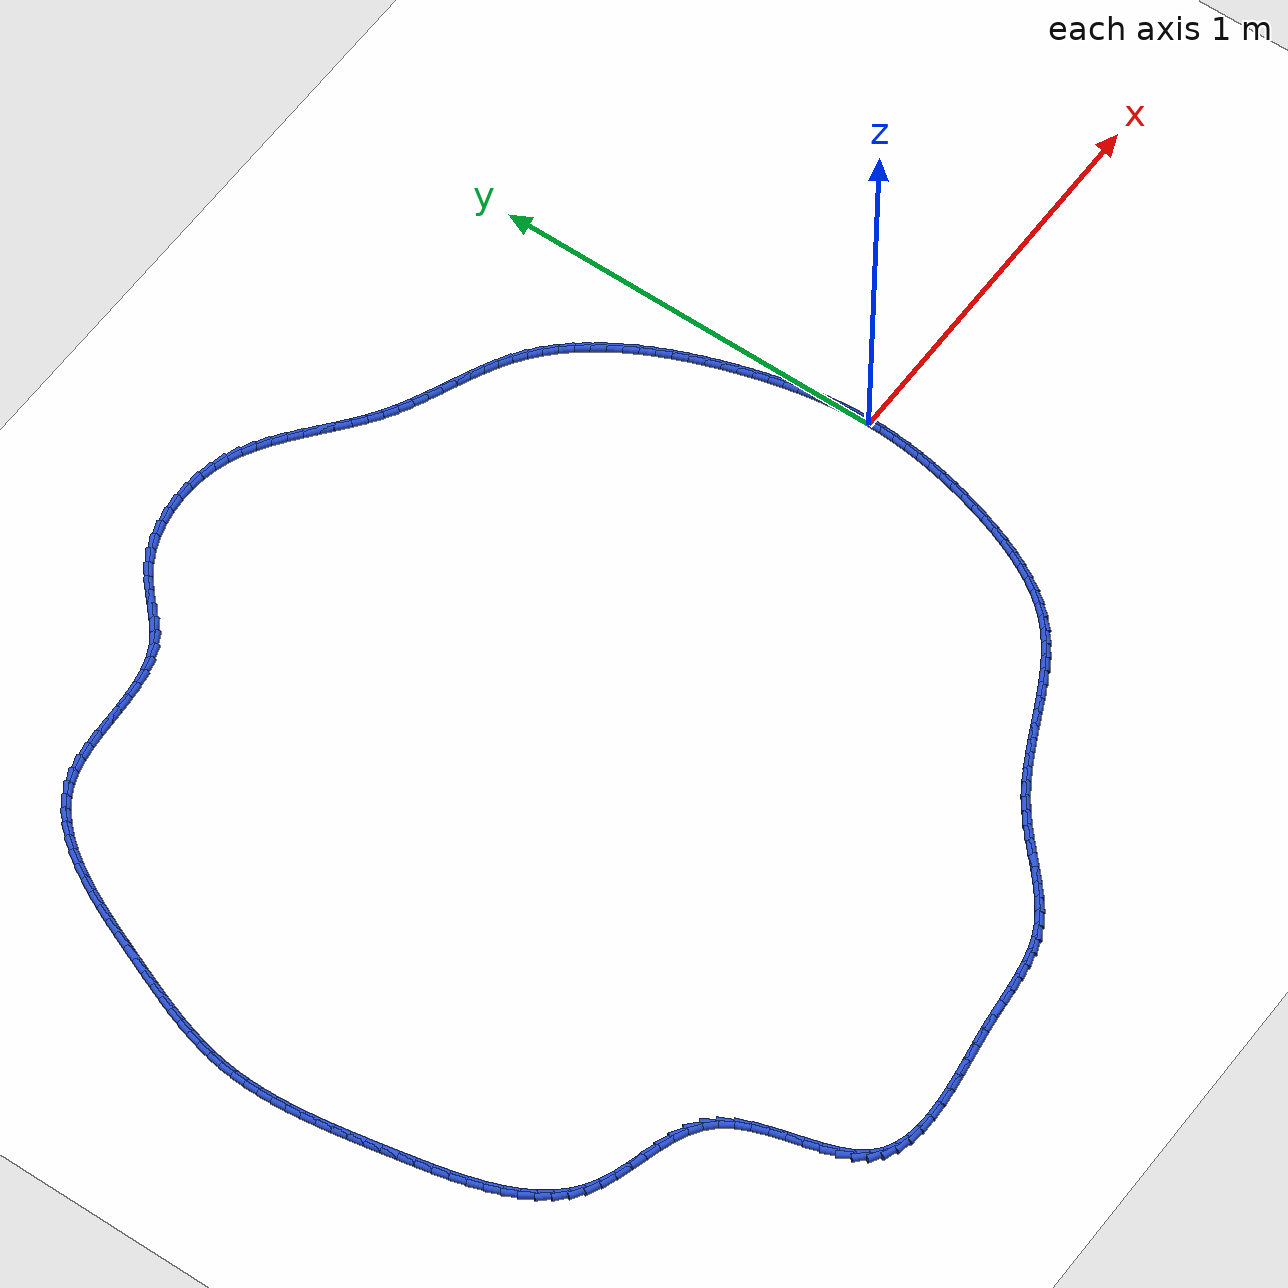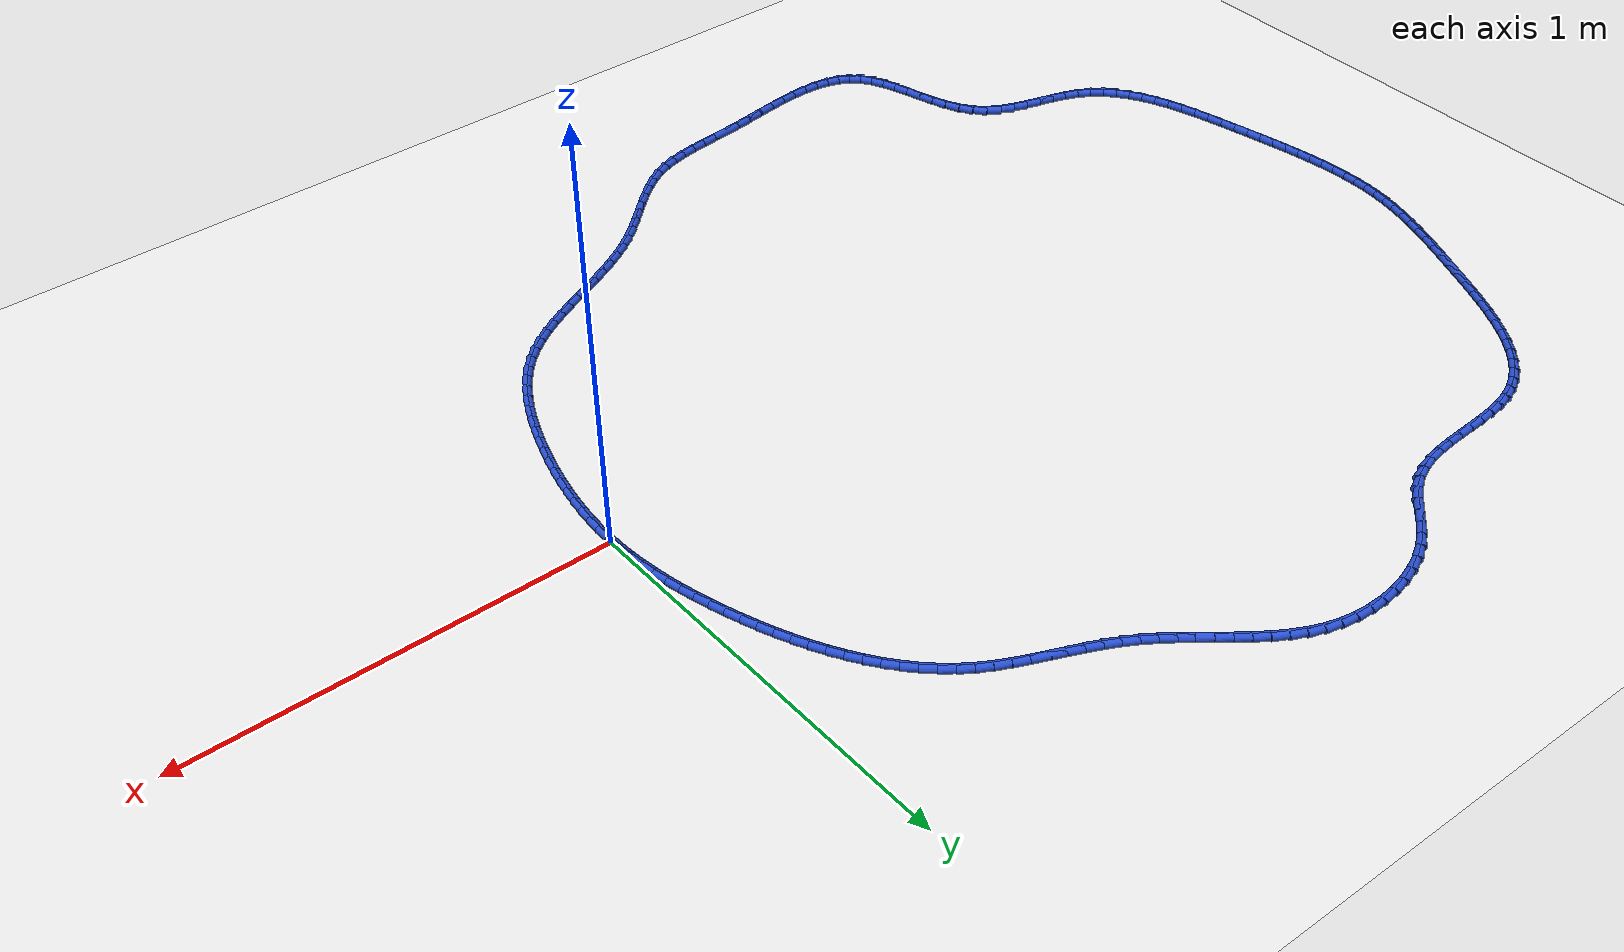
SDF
<sdf version="1.6">
 <world name="default">
  <light name="sun" type="directional">
   <pose>0 0 10 0 -0 0</pose>
   <diffuse>0.8 0.8 0.8 1</diffuse>
   <specular>0.2 0.2 0.2 1</specular>
   <attenuation>
    <range>1000</range>
    <constant>0.9</constant>
    <linear>0.01</linear>
    <quadratic>0.001</quadratic>
   </attenuation>
   <direction>-0.5 0.1 -0.9</direction>
  </light>
  <model name="ground_plane">
   <static>1</static>
   <link name="link">
    <collision name="collision">
     <geometry><plane><normal>0 0 1</normal><size>100 100</size></plane></geometry>
     <surface><friction><ode><mu>100</mu><mu2>50</mu2></ode></friction></surface>
    </collision>
    <visual name="visual">
     <cast_shadows>0</cast_shadows>
     <geometry><plane><normal>0 0 1</normal><size>100 100</size></plane></geometry>
     <material>
      <script><uri>file://media/materials/scripts/gazebo.material</uri><name>Gazebo/WhiteGlow</name></script>
     </material>
    </visual>
   </link>
  </model>
  <gravity>0 0 -9.8</gravity>
  <magnetic_field>6e-06 2.3e-05 -4.2e-05</magnetic_field>
  <atmosphere type="adiabatic"/>
  <physics name="default_physics" default="0" type="ode">
   <max_step_size>0.001</max_step_size>
   <real_time_factor>1</real_time_factor>
   <real_time_update_rate>1000</real_time_update_rate>
  </physics>
  <scene><ambient>0.4 0.4 0.4 1</ambient><background>0.7 0.7 0.7 1</background><shadows>1</shadows></scene>
  <spherical_coordinates>
   <surface_model>EARTH_WGS84</surface_model>
   <latitude_deg>0</latitude_deg>
   <longitude_deg>0</longitude_deg>
   <elevation>0</elevation>
   <heading_deg>0</heading_deg>
  </spherical_coordinates>
  <model name="line">
   <link name="link_0">
    <pose>-3.469446951953614e-18 -1.1796119636642288e-16 0.01 0 1.57 -1.5491380946228126</pose>
    <collision name="collision">
     <geometry><cylinder><radius>0.01</radius><length>0.08</length></cylinder></geometry>
    </collision>
    <visual name="visual">
     <material>
      <script><name>Gazebo/Blue</name><uri>file://media/materials/scripts/gazebo.material</uri></script>
     </material>
     <geometry><cylinder><radius>0.01</radius><length>0.08</length></cylinder></geometry>
    </visual>
   </link>
   <link name="link_1">
    <pose>-0.0007798753378044431 0.03600263339787785 0.01 0 1.57 -1.5088348567655554</pose>
    <collision name="collision">
     <geometry><cylinder><radius>0.01</radius><length>0.08</length></cylinder></geometry>
    </collision>
    <visual name="visual">
     <material>
      <script><name>Gazebo/Blue</name><uri>file://media/materials/scripts/gazebo.material</uri></script>
     </material>
     <geometry><cylinder><radius>0.01</radius><length>0.08</length></cylinder></geometry>
    </visual>
   </link>
   <link name="link_2">
    <pose>-0.0030126451728320043 0.07199131692479639 0.01 0 1.57 -1.4704603669537422</pose>
    <collision name="collision">
     <geometry><cylinder><radius>0.01</radius><length>0.08</length></cylinder></geometry>
    </collision>
    <visual name="visual">
     <material>
      <script><name>Gazebo/Blue</name><uri>file://media/materials/scripts/gazebo.material</uri></script>
     </material>
     <geometry><cylinder><radius>0.01</radius><length>0.08</length></cylinder></geometry>
    </visual>
   </link>
   <link name="link_3">
    <pose>-0.006635128885073642 0.10797362412059247 0.01 0 1.57 -1.4341181131902399</pose>
    <collision name="collision">
     <geometry><cylinder><radius>0.01</radius><length>0.08</length></cylinder></geometry>
    </collision>
    <visual name="visual">
     <material>
      <script><name>Gazebo/Blue</name><uri>file://media/materials/scripts/gazebo.material</uri></script>
     </material>
     <geometry><cylinder><radius>0.01</radius><length>0.08</length></cylinder></geometry>
    </visual>
   </link>
   <link name="link_4">
    <pose>-0.011584145854520302 0.14395712852510292 0.01 0 1.57 -1.3998775129006569</pose>
    <collision name="collision">
     <geometry><cylinder><radius>0.01</radius><length>0.08</length></cylinder></geometry>
    </collision>
    <visual name="visual">
     <material>
      <script><name>Gazebo/Blue</name><uri>file://media/materials/scripts/gazebo.material</uri></script>
     </material>
     <geometry><cylinder><radius>0.01</radius><length>0.08</length></cylinder></geometry>
    </visual>
   </link>
   <link name="link_5">
    <pose>-0.017796515461162947 0.1799494036781647 0.01 0 1.57 -1.367777689535852</pose>
    <collision name="collision">
     <geometry><cylinder><radius>0.01</radius><length>0.08</length></cylinder></geometry>
    </collision>
    <visual name="visual">
     <material>
      <script><name>Gazebo/Blue</name><uri>file://media/materials/scripts/gazebo.material</uri></script>
     </material>
     <geometry><cylinder><radius>0.01</radius><length>0.08</length></cylinder></geometry>
    </visual>
   </link>
   <link name="link_6">
    <pose>-0.02520905708499252 0.21595802311961457 0.01 0 1.57 -1.3378318157825284</pose>
    <collision name="collision">
     <geometry><cylinder><radius>0.01</radius><length>0.08</length></cylinder></geometry>
    </collision>
    <visual name="visual">
     <material>
      <script><name>Gazebo/Blue</name><uri>file://media/materials/scripts/gazebo.material</uri></script>
     </material>
     <geometry><cylinder><radius>0.01</radius><length>0.08</length></cylinder></geometry>
    </visual>
   </link>
   <link name="link_7">
    <pose>-0.03375859010599997 0.2519905603892895 0.01 0 1.57 -1.3100316401068735</pose>
    <collision name="collision">
     <geometry><cylinder><radius>0.01</radius><length>0.08</length></cylinder></geometry>
    </collision>
    <visual name="visual">
     <material>
      <script><name>Gazebo/Blue</name><uri>file://media/materials/scripts/gazebo.material</uri></script>
     </material>
     <geometry><cylinder><radius>0.01</radius><length>0.08</length></cylinder></geometry>
    </visual>
   </link>
   <link name="link_8">
    <pose>-0.043381933904176266 0.28805458902702635 0.01 0 1.57 -1.2843519016128713</pose>
    <collision name="collision">
     <geometry><cylinder><radius>0.01</radius><length>0.08</length></cylinder></geometry>
    </collision>
    <visual name="visual">
     <material>
      <script><name>Gazebo/Blue</name><uri>file://media/materials/scripts/gazebo.material</uri></script>
     </material>
     <geometry><cylinder><radius>0.01</radius><length>0.08</length></cylinder></geometry>
    </visual>
   </link>
   <link name="link_9">
    <pose>-0.054015907859512366 0.3241576825726622 0.01 0 1.57 -1.2600398146654306</pose>
    <collision name="collision">
     <geometry><cylinder><radius>0.01</radius><length>0.08</length></cylinder></geometry>
    </collision>
    <visual name="visual">
     <material>
      <script><name>Gazebo/Blue</name><uri>file://media/materials/scripts/gazebo.material</uri></script>
     </material>
     <geometry><cylinder><radius>0.01</radius><length>0.08</length></cylinder></geometry>
    </visual>
   </link>
   <link name="link_10">
    <pose>-0.0656164149120683 0.36027812225615513 0.01 0 1.57 -1.2339961770029053</pose>
    <collision name="collision">
     <geometry><cylinder><radius>0.01</radius><length>0.08</length></cylinder></geometry>
    </collision>
    <visual name="visual">
     <material>
      <script><name>Gazebo/Blue</name><uri>file://media/materials/scripts/gazebo.material</uri></script>
     </material>
     <geometry><cylinder><radius>0.01</radius><length>0.08</length></cylinder></geometry>
    </visual>
   </link>
   <link name="link_11">
    <pose>-0.07821920557809857 0.3962716272731024 0.01 0 1.57 -1.205217569808733</pose>
    <collision name="collision">
     <geometry><cylinder><radius>0.01</radius><length>0.08</length></cylinder></geometry>
    </collision>
    <visual name="visual">
     <material>
      <script><name>Gazebo/Blue</name><uri>file://media/materials/scripts/gazebo.material</uri></script>
     </material>
     <geometry><cylinder><radius>0.01</radius><length>0.08</length></cylinder></geometry>
    </visual>
   </link>
   <link name="link_12">
    <pose>-0.09188091065348353 0.43196186663460007 0.01 0 1.57 -1.1734392270744438</pose>
    <collision name="collision">
     <geometry><cylinder><radius>0.01</radius><length>0.08</length></cylinder></geometry>
    </collision>
    <visual name="visual">
     <material>
      <script><name>Gazebo/Blue</name><uri>file://media/materials/scripts/gazebo.material</uri></script>
     </material>
     <geometry><cylinder><radius>0.01</radius><length>0.08</length></cylinder></geometry>
    </visual>
   </link>
   <link name="link_13">
    <pose>-0.10665816100146167 0.4671725092483526 0.01 0 1.57 -1.1383623896500155</pose>
    <collision name="collision">
     <geometry><cylinder><radius>0.01</radius><length>0.08</length></cylinder></geometry>
    </collision>
    <visual name="visual">
     <material>
      <script><name>Gazebo/Blue</name><uri>file://media/materials/scripts/gazebo.material</uri></script>
     </material>
     <geometry><cylinder><radius>0.01</radius><length>0.08</length></cylinder></geometry>
    </visual>
   </link>
   <link name="link_14">
    <pose>-0.1226075874852716 0.5017272240220647 0.01 0 1.57 -1.0996566863807242</pose>
    <collision name="collision">
     <geometry><cylinder><radius>0.01</radius><length>0.08</length></cylinder></geometry>
    </collision>
    <visual name="visual">
     <material>
      <script><name>Gazebo/Blue</name><uri>file://media/materials/scripts/gazebo.material</uri></script>
     </material>
     <geometry><cylinder><radius>0.01</radius><length>0.08</length></cylinder></geometry>
    </visual>
   </link>
   <link name="link_15">
    <pose>-0.13978582096815192 0.535449679863441 0.01 0 1.57 -1.0569655152053576</pose>
    <collision name="collision">
     <geometry><cylinder><radius>0.01</radius><length>0.08</length></cylinder></geometry>
    </collision>
    <visual name="visual">
     <material>
      <script><name>Gazebo/Blue</name><uri>file://media/materials/scripts/gazebo.material</uri></script>
     </material>
     <geometry><cylinder><radius>0.01</radius><length>0.08</length></cylinder></geometry>
    </visual>
   </link>
   <link name="link_16">
    <pose>-0.15824949231334112 0.568163545680186 0.01 0 1.57 -1.0099160939286953</pose>
    <collision name="collision">
     <geometry><cylinder><radius>0.01</radius><length>0.08</length></cylinder></geometry>
    </collision>
    <visual name="visual">
     <material>
      <script><name>Gazebo/Blue</name><uri>file://media/materials/scripts/gazebo.material</uri></script>
     </material>
     <geometry><cylinder><radius>0.01</radius><length>0.08</length></cylinder></geometry>
    </visual>
   </link>
   <link name="link_17">
    <pose>-0.17805523238407775 0.5996924903800042 0.01 0 1.57 -0.958136275318392</pose>
    <collision name="collision">
     <geometry><cylinder><radius>0.01</radius><length>0.08</length></cylinder></geometry>
    </collision>
    <visual name="visual">
     <material>
      <script><name>Gazebo/Blue</name><uri>file://media/materials/scripts/gazebo.material</uri></script>
     </material>
     <geometry><cylinder><radius>0.01</radius><length>0.08</length></cylinder></geometry>
    </visual>
   </link>
   <link name="link_18">
    <pose>-0.19925967204360048 0.6298601828706004 0.01 0 1.57 -0.9012804884405026</pose>
    <collision name="collision">
     <geometry><cylinder><radius>0.01</radius><length>0.08</length></cylinder></geometry>
    </collision>
    <visual name="visual">
     <material>
      <script><name>Gazebo/Blue</name><uri>file://media/materials/scripts/gazebo.material</uri></script>
     </material>
     <geometry><cylinder><radius>0.01</radius><length>0.08</length></cylinder></geometry>
    </visual>
   </link>
   <link name="link_19">
    <pose>-0.22191944215514767 0.6584902920596791 0.01 0 1.57 -0.8390669667489712</pose>
    <collision name="collision">
     <geometry><cylinder><radius>0.01</radius><length>0.08</length></cylinder></geometry>
    </collision>
    <visual name="visual">
     <material>
      <script><name>Gazebo/Blue</name><uri>file://media/materials/scripts/gazebo.material</uri></script>
     </material>
     <geometry><cylinder><radius>0.01</radius><length>0.08</length></cylinder></geometry>
    </visual>
   </link>
   <link name="link_20">
    <pose>-0.24609117358195798 0.6854064868549445 0.01 0 1.57 -0.7713272634052497</pose>
    <collision name="collision">
     <geometry><cylinder><radius>0.01</radius><length>0.08</length></cylinder></geometry>
    </collision>
    <visual name="visual">
     <material>
      <script><name>Gazebo/Blue</name><uri>file://media/materials/scripts/gazebo.material</uri></script>
     </material>
     <geometry><cylinder><radius>0.01</radius><length>0.08</length></cylinder></geometry>
    </visual>
   </link>
   <link name="link_21">
    <pose>-0.2718314971872702 0.710432436164102 0.01 0 1.57 -0.6980663497602803</pose>
    <collision name="collision">
     <geometry><cylinder><radius>0.01</radius><length>0.08</length></cylinder></geometry>
    </collision>
    <visual name="visual">
     <material>
      <script><name>Gazebo/Blue</name><uri>file://media/materials/scripts/gazebo.material</uri></script>
     </material>
     <geometry><cylinder><radius>0.01</radius><length>0.08</length></cylinder></geometry>
    </visual>
   </link>
   <link name="link_22">
    <pose>-0.29919704383432244 0.7333918088948556 0.01 0 1.57 -0.6196539736845612</pose>
    <collision name="collision">
     <geometry><cylinder><radius>0.01</radius><length>0.08</length></cylinder></geometry>
    </collision>
    <visual name="visual">
     <material>
      <script><name>Gazebo/Blue</name><uri>file://media/materials/scripts/gazebo.material</uri></script>
     </material>
     <geometry><cylinder><radius>0.01</radius><length>0.08</length></cylinder></geometry>
    </visual>
   </link>
   <link name="link_23">
    <pose>-0.3282421768702616 0.754112221997207 0.01 0 1.57 -0.5445846375043158</pose>
    <collision name="collision">
     <geometry><cylinder><radius>0.01</radius><length>0.08</length></cylinder></geometry>
    </collision>
    <visual name="visual">
     <material>
      <script><name>Gazebo/Blue</name><uri>file://media/materials/scripts/gazebo.material</uri></script>
     </material>
     <geometry><cylinder><radius>0.01</radius><length>0.08</length></cylinder></geometry>
    </visual>
   </link>
   <link name="link_24">
    <pose>-0.3588792933622943 0.7726684742955864 0.01 0 1.57 -0.48587849276729356</pose>
    <collision name="collision">
     <geometry><cylinder><radius>0.01</radius><length>0.08</length></cylinder></geometry>
    </collision>
    <visual name="visual">
     <material>
      <script><name>Gazebo/Blue</name><uri>file://media/materials/scripts/gazebo.material</uri></script>
     </material>
     <geometry><cylinder><radius>0.01</radius><length>0.08</length></cylinder></geometry>
    </visual>
   </link>
   <link name="link_25">
    <pose>-0.39079727221336463 0.7895245389932632 0.01 0 1.57 -0.4444831121165945</pose>
    <collision name="collision">
     <geometry><cylinder><radius>0.01</radius><length>0.08</length></cylinder></geometry>
    </collision>
    <visual name="visual">
     <material>
      <script><name>Gazebo/Blue</name><uri>file://media/materials/scripts/gazebo.material</uri></script>
     </material>
     <geometry><cylinder><radius>0.01</radius><length>0.08</length></cylinder></geometry>
    </visual>
   </link>
   <link name="link_26">
    <pose>-0.4236653535442671 0.8051785829836233 0.01 0 1.57 -0.4198910959469405</pose>
    <collision name="collision">
     <geometry><cylinder><radius>0.01</radius><length>0.08</length></cylinder></geometry>
    </collision>
    <visual name="visual">
     <material>
      <script><name>Gazebo/Blue</name><uri>file://media/materials/scripts/gazebo.material</uri></script>
     </material>
     <geometry><cylinder><radius>0.01</radius><length>0.08</length></cylinder></geometry>
    </visual>
   </link>
   <link name="link_27">
    <pose>-0.45715277747579525 0.8201287731600525 0.01 0 1.57 -0.41160252978669476</pose>
    <collision name="collision">
     <geometry><cylinder><radius>0.01</radius><length>0.08</length></cylinder></geometry>
    </collision>
    <visual name="visual">
     <material>
      <script><name>Gazebo/Blue</name><uri>file://media/materials/scripts/gazebo.material</uri></script>
     </material>
     <geometry><cylinder><radius>0.01</radius><length>0.08</length></cylinder></geometry>
    </visual>
   </link>
   <link name="link_28">
    <pose>-0.4909287841287434 0.8348732764159369 0.01 0 1.57 -0.41931719088102754</pose>
    <collision name="collision">
     <geometry><cylinder><radius>0.01</radius><length>0.08</length></cylinder></geometry>
    </collision>
    <visual name="visual">
     <material>
      <script><name>Gazebo/Blue</name><uri>file://media/materials/scripts/gazebo.material</uri></script>
     </material>
     <geometry><cylinder><radius>0.01</radius><length>0.08</length></cylinder></geometry>
    </visual>
   </link>
   <link name="link_29">
    <pose>-0.5246626136239061 0.8499102596446625 0.01 0 1.57 -0.4429885939198672</pose>
    <collision name="collision">
     <geometry><cylinder><radius>0.01</radius><length>0.08</length></cylinder></geometry>
    </collision>
    <visual name="visual">
     <material>
      <script><name>Gazebo/Blue</name><uri>file://media/materials/scripts/gazebo.material</uri></script>
     </material>
     <geometry><cylinder><radius>0.01</radius><length>0.08</length></cylinder></geometry>
    </visual>
   </link>
   <link name="link_30">
    <pose>-0.5580235060820768 0.8657378897396151 0.01 0 1.57 -0.48276060589552855</pose>
    <collision name="collision">
     <geometry><cylinder><radius>0.01</radius><length>0.08</length></cylinder></geometry>
    </collision>
    <visual name="visual">
     <material>
      <script><name>Gazebo/Blue</name><uri>file://media/materials/scripts/gazebo.material</uri></script>
     </material>
     <geometry><cylinder><radius>0.01</radius><length>0.08</length></cylinder></geometry>
    </visual>
   </link>
   <link name="link_31">
    <pose>-0.5906807016240501 0.8828543335941806 0.01 0 1.57 -0.5386801775550785</pose>
    <collision name="collision">
     <geometry><cylinder><radius>0.01</radius><length>0.08</length></cylinder></geometry>
    </collision>
    <visual name="visual">
     <material>
      <script><name>Gazebo/Blue</name><uri>file://media/materials/scripts/gazebo.material</uri></script>
     </material>
     <geometry><cylinder><radius>0.01</radius><length>0.08</length></cylinder></geometry>
    </visual>
   </link>
   <link name="link_32">
    <pose>-0.6223054388526957 0.9017544461950724 0.01 0 1.57 -0.5998490313299457</pose>
    <collision name="collision">
     <geometry><cylinder><radius>0.01</radius><length>0.08</length></cylinder></geometry>
    </collision>
    <visual name="visual">
     <material>
      <script><name>Gazebo/Blue</name><uri>file://media/materials/scripts/gazebo.material</uri></script>
     </material>
     <geometry><cylinder><radius>0.01</radius><length>0.08</length></cylinder></geometry>
    </visual>
   </link>
   <link name="link_33">
    <pose>-0.6527743945038681 0.922592628175387 0.01 0 1.57 -0.6461284967187175</pose>
    <collision name="collision">
     <geometry><cylinder><radius>0.01</radius><length>0.08</length></cylinder></geometry>
    </collision>
    <visual name="visual">
     <material>
      <script><name>Gazebo/Blue</name><uri>file://media/materials/scripts/gazebo.material</uri></script>
     </material>
     <geometry><cylinder><radius>0.01</radius><length>0.08</length></cylinder></geometry>
    </visual>
   </link>
   <link name="link_34">
    <pose>-0.6823450294410981 0.9448922404864786 0.01 0 1.57 -0.6755627695601314</pose>
    <collision name="collision">
     <geometry><cylinder><radius>0.01</radius><length>0.08</length></cylinder></geometry>
    </collision>
    <visual name="visual">
     <material>
      <script><name>Gazebo/Blue</name><uri>file://media/materials/scripts/gazebo.material</uri></script>
     </material>
     <geometry><cylinder><radius>0.01</radius><length>0.08</length></cylinder></geometry>
    </visual>
   </link>
   <link name="link_35">
    <pose>-0.7113161158697496 0.9681081824656042 0.01 0 1.57 -0.6884321826403728</pose>
    <collision name="collision">
     <geometry><cylinder><radius>0.01</radius><length>0.08</length></cylinder></geometry>
    </collision>
    <visual name="visual">
     <material>
      <script><name>Gazebo/Blue</name><uri>file://media/materials/scripts/gazebo.material</uri></script>
     </material>
     <geometry><cylinder><radius>0.01</radius><length>0.08</length></cylinder></geometry>
    </visual>
   </link>
   <link name="link_36">
    <pose>-0.7399864259951874 0.9916953534500205 0.01 0 1.57 -0.6848390199379392</pose>
    <collision name="collision">
     <geometry><cylinder><radius>0.01</radius><length>0.08</length></cylinder></geometry>
    </collision>
    <visual name="visual">
     <material>
      <script><name>Gazebo/Blue</name><uri>file://media/materials/scripts/gazebo.material</uri></script>
     </material>
     <geometry><cylinder><radius>0.01</radius><length>0.08</length></cylinder></geometry>
    </visual>
   </link>
   <link name="link_37">
    <pose>-0.7686547320227759 1.0151086527769853 0.01 0 1.57 -0.6646027736693845</pose>
    <collision name="collision">
     <geometry><cylinder><radius>0.01</radius><length>0.08</length></cylinder></geometry>
    </collision>
    <visual name="visual">
     <material>
      <script><name>Gazebo/Blue</name><uri>file://media/materials/scripts/gazebo.material</uri></script>
     </material>
     <geometry><cylinder><radius>0.01</radius><length>0.08</length></cylinder></geometry>
    </visual>
   </link>
   <link name="link_38">
    <pose>-0.7976198061578796 1.0378029797837554 0.01 0 1.57 -0.6272817728584842</pose>
    <collision name="collision">
     <geometry><cylinder><radius>0.01</radius><length>0.08</length></cylinder></geometry>
    </collision>
    <visual name="visual">
     <material>
      <script><name>Gazebo/Blue</name><uri>file://media/materials/scripts/gazebo.material</uri></script>
     </material>
     <geometry><cylinder><radius>0.01</radius><length>0.08</length></cylinder></geometry>
    </visual>
   </link>
   <link name="link_39">
    <pose>-0.8271804206058635 1.0592332338075883 0.01 0 1.57 -0.5723338704626014</pose>
    <collision name="collision">
     <geometry><cylinder><radius>0.01</radius><length>0.08</length></cylinder></geometry>
    </collision>
    <visual name="visual">
     <material>
      <script><name>Gazebo/Blue</name><uri>file://media/materials/scripts/gazebo.material</uri></script>
     </material>
     <geometry><cylinder><radius>0.01</radius><length>0.08</length></cylinder></geometry>
    </visual>
   </link>
   <link name="link_40">
    <pose>-0.8576353475720917 1.078854314185741 0.01 0 1.57 -0.4994503161614712</pose>
    <collision name="collision">
     <geometry><cylinder><radius>0.01</radius><length>0.08</length></cylinder></geometry>
    </collision>
    <visual name="visual">
     <material>
      <script><name>Gazebo/Blue</name><uri>file://media/materials/scripts/gazebo.material</uri></script>
     </material>
     <geometry><cylinder><radius>0.01</radius><length>0.08</length></cylinder></geometry>
    </visual>
   </link>
   <link name="link_41">
    <pose>-0.8892833592619287 1.0961211202554706 0.01 0 1.57 -0.4090811106167614</pose>
    <collision name="collision">
     <geometry><cylinder><radius>0.01</radius><length>0.08</length></cylinder></geometry>
    </collision>
    <visual name="visual">
     <material>
      <script><name>Gazebo/Blue</name><uri>file://media/materials/scripts/gazebo.material</uri></script>
     </material>
     <geometry><cylinder><radius>0.01</radius><length>0.08</length></cylinder></geometry>
    </visual>
   </link>
   <link name="link_42">
    <pose>-0.9224232278807389 1.1104885513540341 0.01 0 1.57 -0.30399746329364485</pose>
    <collision name="collision">
     <geometry><cylinder><radius>0.01</radius><length>0.08</length></cylinder></geometry>
    </collision>
    <visual name="visual">
     <material>
      <script><name>Gazebo/Blue</name><uri>file://media/materials/scripts/gazebo.material</uri></script>
     </material>
     <geometry><cylinder><radius>0.01</radius><length>0.08</length></cylinder></geometry>
    </visual>
   </link>
   <link name="link_43">
    <pose>-0.9573178319602756 1.121435744890637 0.01 0 1.57 -0.1979942934456531</pose>
    <collision name="collision">
     <geometry><cylinder><radius>0.01</radius><length>0.08</length></cylinder></geometry>
    </collision>
    <visual name="visual">
     <material>
      <script><name>Gazebo/Blue</name><uri>file://media/materials/scripts/gazebo.material</uri></script>
     </material>
     <geometry><cylinder><radius>0.01</radius><length>0.08</length></cylinder></geometry>
    </visual>
   </link>
   <link name="link_44">
    <pose>-0.9937741315726573 1.128749708250298 0.01 0 1.57 -0.09777769361011011</pose>
    <collision name="collision">
     <geometry><cylinder><radius>0.01</radius><length>0.08</length></cylinder></geometry>
    </collision>
    <visual name="visual">
     <material>
      <script><name>Gazebo/Blue</name><uri>file://media/materials/scripts/gazebo.material</uri></script>
     </material>
     <geometry><cylinder><radius>0.01</radius><length>0.08</length></cylinder></geometry>
    </visual>
   </link>
   <link name="link_45">
    <pose>-1.031285485926691 1.1324292153920001 0.01 0 1.57 -0.0012612365559044373</pose>
    <collision name="collision">
     <geometry><cylinder><radius>0.01</radius><length>0.08</length></cylinder></geometry>
    </collision>
    <visual name="visual">
     <material>
      <script><name>Gazebo/Blue</name><uri>file://media/materials/scripts/gazebo.material</uri></script>
     </material>
     <geometry><cylinder><radius>0.01</radius><length>0.08</length></cylinder></geometry>
    </visual>
   </link>
   <link name="link_46">
    <pose>-1.06933907936797 1.1324772100005804 0.01 0 1.57 0.09374465614290557</pose>
    <collision name="collision">
     <geometry><cylinder><radius>0.01</radius><length>0.08</length></cylinder></geometry>
    </collision>
    <visual name="visual">
     <material>
      <script><name>Gazebo/Blue</name><uri>file://media/materials/scripts/gazebo.material</uri></script>
     </material>
     <geometry><cylinder><radius>0.01</radius><length>0.08</length></cylinder></geometry>
    </visual>
   </link>
   <link name="link_47">
    <pose>-1.1074220962420882 1.1288966357608752 0.01 0 1.57 0.18935990852704834</pose>
    <collision name="collision">
     <geometry><cylinder><radius>0.01</radius><length>0.08</length></cylinder></geometry>
    </collision>
    <visual name="visual">
     <material>
      <script><name>Gazebo/Blue</name><uri>file://media/materials/scripts/gazebo.material</uri></script>
     </material>
     <geometry><cylinder><radius>0.01</radius><length>0.08</length></cylinder></geometry>
    </visual>
   </link>
   <link name="link_48">
    <pose>-1.1450217208946392 1.1216904363577207 0.01 0 1.57 0.2876390914101385</pose>
    <collision name="collision">
     <geometry><cylinder><radius>0.01</radius><length>0.08</length></cylinder></geometry>
    </collision>
    <visual name="visual">
     <material>
      <script><name>Gazebo/Blue</name><uri>file://media/materials/scripts/gazebo.material</uri></script>
     </material>
     <geometry><cylinder><radius>0.01</radius><length>0.08</length></cylinder></geometry>
    </visual>
   </link>
   <link name="link_49">
    <pose>-1.1816251376712164 1.110861555475954 0.01 0 1.57 0.39055797815319265</pose>
    <collision name="collision">
     <geometry><cylinder><radius>0.01</radius><length>0.08</length></cylinder></geometry>
    </collision>
    <visual name="visual">
     <material>
      <script><name>Gazebo/Blue</name><uri>file://media/materials/scripts/gazebo.material</uri></script>
     </material>
     <geometry><cylinder><radius>0.01</radius><length>0.08</length></cylinder></geometry>
    </visual>
   </link>
   <link name="link_50">
    <pose>-1.216719530917414 1.096412936800411 0.01 0 1.57 0.4999486316795127</pose>
    <collision name="collision">
     <geometry><cylinder><radius>0.01</radius><length>0.08</length></cylinder></geometry>
    </collision>
    <visual name="visual">
     <material>
      <script><name>Gazebo/Blue</name><uri>file://media/materials/scripts/gazebo.material</uri></script>
     </material>
     <geometry><cylinder><radius>0.01</radius><length>0.08</length></cylinder></geometry>
    </visual>
   </link>
   <link name="link_51">
    <pose>-1.2497920849788244 1.0783475240159277 0.01 0 1.57 0.6164669470590998</pose>
    <collision name="collision">
     <geometry><cylinder><radius>0.01</radius><length>0.08</length></cylinder></geometry>
    </collision>
    <visual name="visual">
     <material>
      <script><name>Gazebo/Blue</name><uri>file://media/materials/scripts/gazebo.material</uri></script>
     </material>
     <geometry><cylinder><radius>0.01</radius><length>0.08</length></cylinder></geometry>
    </visual>
   </link>
   <link name="link_52">
    <pose>-1.2803528483238154 1.0566925132489717 0.01 0 1.57 0.7141509189044492</pose>
    <collision name="collision">
     <geometry><cylinder><radius>0.01</radius><length>0.08</length></cylinder></geometry>
    </collision>
    <visual name="visual">
     <material>
      <script><name>Gazebo/Blue</name><uri>file://media/materials/scripts/gazebo.material</uri></script>
     </material>
     <geometry><cylinder><radius>0.01</radius><length>0.08</length></cylinder></geometry>
    </visual>
   </link>
   <link name="link_53">
    <pose>-1.308601896143417 1.032207026052627 0.01 0 1.57 0.7622191861165557</pose>
    <collision name="collision">
     <geometry><cylinder><radius>0.01</radius><length>0.08</length></cylinder></geometry>
    </collision>
    <visual name="visual">
     <material>
      <script><name>Gazebo/Blue</name><uri>file://media/materials/scripts/gazebo.material</uri></script>
     </material>
     <geometry><cylinder><radius>0.01</radius><length>0.08</length></cylinder></geometry>
    </visual>
   </link>
   <link name="link_54">
    <pose>-1.3355351087915779 1.0064943107568707 0.01 0 1.57 0.7590784428358198</pose>
    <collision name="collision">
     <geometry><cylinder><radius>0.01</radius><length>0.08</length></cylinder></geometry>
    </collision>
    <visual name="visual">
     <material>
      <script><name>Gazebo/Blue</name><uri>file://media/materials/scripts/gazebo.material</uri></script>
     </material>
     <geometry><cylinder><radius>0.01</radius><length>0.08</length></cylinder></geometry>
    </visual>
   </link>
   <link name="link_55">
    <pose>-1.3621925214271149 0.9812044515943027 0.01 0 1.57 0.7025540852972219</pose>
    <collision name="collision">
     <geometry><cylinder><radius>0.01</radius><length>0.08</length></cylinder></geometry>
    </collision>
    <visual name="visual">
     <material>
      <script><name>Gazebo/Blue</name><uri>file://media/materials/scripts/gazebo.material</uri></script>
     </material>
     <geometry><cylinder><radius>0.01</radius><length>0.08</length></cylinder></geometry>
    </visual>
   </link>
   <link name="link_56">
    <pose>-1.3896141692088417 0.9579875327975215 0.01 0 1.57 0.5882410393197448</pose>
    <collision name="collision">
     <geometry><cylinder><radius>0.01</radius><length>0.08</length></cylinder></geometry>
    </collision>
    <visual name="visual">
     <material>
      <script><name>Gazebo/Blue</name><uri>file://media/materials/scripts/gazebo.material</uri></script>
     </material>
     <geometry><cylinder><radius>0.01</radius><length>0.08</length></cylinder></geometry>
    </visual>
   </link>
   <link name="link_57">
    <pose>-1.4188400366629559 0.9384935539610495 0.01 0 1.57 0.43142510996842376</pose>
    <collision name="collision">
     <geometry><cylinder><radius>0.01</radius><length>0.08</length></cylinder></geometry>
    </collision>
    <visual name="visual">
     <material>
      <script><name>Gazebo/Blue</name><uri>file://media/materials/scripts/gazebo.material</uri></script>
     </material>
     <geometry><cylinder><radius>0.01</radius><length>0.08</length></cylinder></geometry>
    </visual>
   </link>
   <link name="link_58">
    <pose>-1.4506088255871925 0.9238688869460902 0.01 0 1.57 0.2938625230957346</pose>
    <collision name="collision">
     <geometry><cylinder><radius>0.01</radius><length>0.08</length></cylinder></geometry>
    </collision>
    <visual name="visual">
     <material>
      <script><name>Gazebo/Blue</name><uri>file://media/materials/scripts/gazebo.material</uri></script>
     </material>
     <geometry><cylinder><radius>0.01</radius><length>0.08</length></cylinder></geometry>
    </visual>
   </link>
   <link name="link_59">
    <pose>-1.4846471410567434 0.9135680708928889 0.01 0 1.57 0.1896764735030521</pose>
    <collision name="collision">
     <geometry><cylinder><radius>0.01</radius><length>0.08</length></cylinder></geometry>
    </collision>
    <visual name="visual">
     <material>
      <script><name>Gazebo/Blue</name><uri>file://media/materials/scripts/gazebo.material</uri></script>
     </material>
     <geometry><cylinder><radius>0.01</radius><length>0.08</length></cylinder></geometry>
    </visual>
   </link>
   <link name="link_60">
    <pose>-1.5204692972306493 0.9066907769628599 0.01 0 1.57 0.11676343798065089</pose>
    <collision name="collision">
     <geometry><cylinder><radius>0.01</radius><length>0.08</length></cylinder></geometry>
    </collision>
    <visual name="visual">
     <material>
      <script><name>Gazebo/Blue</name><uri>file://media/materials/scripts/gazebo.material</uri></script>
     </material>
     <geometry><cylinder><radius>0.01</radius><length>0.08</length></cylinder></geometry>
    </visual>
   </link>
   <link name="link_61">
    <pose>-1.5575896082679486 0.9023366763174164 0.01 0 1.57 0.07187796368908876</pose>
    <collision name="collision">
     <geometry><cylinder><radius>0.01</radius><length>0.08</length></cylinder></geometry>
    </collision>
    <visual name="visual">
     <material>
      <script><name>Gazebo/Blue</name><uri>file://media/materials/scripts/gazebo.material</uri></script>
     </material>
     <geometry><cylinder><radius>0.01</radius><length>0.08</length></cylinder></geometry>
    </visual>
   </link>
   <link name="link_62">
    <pose>-1.5955223883276815 0.8996054401179723 0.01 0 1.57 0.05245376161355753</pose>
    <collision name="collision">
     <geometry><cylinder><radius>0.01</radius><length>0.08</length></cylinder></geometry>
    </collision>
    <visual name="visual">
     <material>
      <script><name>Gazebo/Blue</name><uri>file://media/materials/scripts/gazebo.material</uri></script>
     </material>
     <geometry><cylinder><radius>0.01</radius><length>0.08</length></cylinder></geometry>
    </visual>
   </link>
   <link name="link_63">
    <pose>-1.6337819515688872 0.8975967395259414 0.01 0 1.57 0.05732442063820508</pose>
    <collision name="collision">
     <geometry><cylinder><radius>0.01</radius><length>0.08</length></cylinder></geometry>
    </collision>
    <visual name="visual">
     <material>
      <script><name>Gazebo/Blue</name><uri>file://media/materials/scripts/gazebo.material</uri></script>
     </material>
     <geometry><cylinder><radius>0.01</radius><length>0.08</length></cylinder></geometry>
    </visual>
   </link>
   <link name="link_64">
    <pose>-1.671882612150605 0.8954102457027369 0.01 0 1.57 0.08693881976616938</pose>
    <collision name="collision">
     <geometry><cylinder><radius>0.01</radius><length>0.08</length></cylinder></geometry>
    </collision>
    <visual name="visual">
     <material>
      <script><name>Gazebo/Blue</name><uri>file://media/materials/scripts/gazebo.material</uri></script>
     </material>
     <geometry><cylinder><radius>0.01</radius><length>0.08</length></cylinder></geometry>
    </visual>
   </link>
   <link name="link_65">
    <pose>-1.7093386842318747 0.892145629809773 0.01 0 1.57 0.1433445897536626</pose>
    <collision name="collision">
     <geometry><cylinder><radius>0.01</radius><length>0.08</length></cylinder></geometry>
    </collision>
    <visual name="visual">
     <material>
      <script><name>Gazebo/Blue</name><uri>file://media/materials/scripts/gazebo.material</uri></script>
     </material>
     <geometry><cylinder><radius>0.01</radius><length>0.08</length></cylinder></geometry>
    </visual>
   </link>
   <link name="link_66">
    <pose>-1.7456644819717355 0.8869025630084632 0.01 0 1.57 0.22985710713564497</pose>
    <collision name="collision">
     <geometry><cylinder><radius>0.01</radius><length>0.08</length></cylinder></geometry>
    </collision>
    <visual name="visual">
     <material>
      <script><name>Gazebo/Blue</name><uri>file://media/materials/scripts/gazebo.material</uri></script>
     </material>
     <geometry><cylinder><radius>0.01</radius><length>0.08</length></cylinder></geometry>
    </visual>
   </link>
   <link name="link_67">
    <pose>-1.7803743195292268 0.8787807164602208 0.01 0 1.57 0.34924841786862143</pose>
    <collision name="collision">
     <geometry><cylinder><radius>0.01</radius><length>0.08</length></cylinder></geometry>
    </collision>
    <visual name="visual">
     <material>
      <script><name>Gazebo/Blue</name><uri>file://media/materials/scripts/gazebo.material</uri></script>
     </material>
     <geometry><cylinder><radius>0.01</radius><length>0.08</length></cylinder></geometry>
    </visual>
   </link>
   <link name="link_68">
    <pose>-1.8129935747464805 0.8669015339209604 0.01 0 1.57 0.4834277409125877</pose>
    <collision name="collision">
     <geometry><cylinder><radius>0.01</radius><length>0.08</length></cylinder></geometry>
    </collision>
    <visual name="visual">
     <material>
      <script><name>Gazebo/Blue</name><uri>file://media/materials/scripts/gazebo.material</uri></script>
     </material>
     <geometry><cylinder><radius>0.01</radius><length>0.08</length></cylinder></geometry>
    </visual>
   </link>
   <link name="link_69">
    <pose>-1.843343439118624 0.8509686007951692 0.01 0 1.57 0.6082505761260839</pose>
    <collision name="collision">
     <geometry><cylinder><radius>0.01</radius><length>0.08</length></cylinder></geometry>
    </collision>
    <visual name="visual">
     <material>
      <script><name>Gazebo/Blue</name><uri>file://media/materials/scripts/gazebo.material</uri></script>
     </material>
     <geometry><cylinder><radius>0.01</radius><length>0.08</length></cylinder></geometry>
    </visual>
   </link>
   <link name="link_70">
    <pose>-1.871565894211452 0.8313167960692662 0.01 0 1.57 0.7195353318911051</pose>
    <collision name="collision">
     <geometry><cylinder><radius>0.01</radius><length>0.08</length></cylinder></geometry>
    </collision>
    <visual name="visual">
     <material>
      <script><name>Gazebo/Blue</name><uri>file://media/materials/scripts/gazebo.material</uri></script>
     </material>
     <geometry><cylinder><radius>0.01</radius><length>0.08</length></cylinder></geometry>
    </visual>
   </link>
   <link name="link_71">
    <pose>-1.8978189908481777 0.8083126219624354 0.01 0 1.57 0.8160884264763613</pose>
    <collision name="collision">
     <geometry><cylinder><radius>0.01</radius><length>0.08</length></cylinder></geometry>
    </collision>
    <visual name="visual">
     <material>
      <script><name>Gazebo/Blue</name><uri>file://media/materials/scripts/gazebo.material</uri></script>
     </material>
     <geometry><cylinder><radius>0.01</radius><length>0.08</length></cylinder></geometry>
    </visual>
   </link>
   <link name="link_72">
    <pose>-1.9222607798520124 0.7823225806938614 0.01 0 1.57 0.8981687948430194</pose>
    <collision name="collision">
     <geometry><cylinder><radius>0.01</radius><length>0.08</length></cylinder></geometry>
    </collision>
    <visual name="visual">
     <material>
      <script><name>Gazebo/Blue</name><uri>file://media/materials/scripts/gazebo.material</uri></script>
     </material>
     <geometry><cylinder><radius>0.01</radius><length>0.08</length></cylinder></geometry>
    </visual>
   </link>
   <link name="link_73">
    <pose>-1.9450493120461685 0.7537131744827295 0.01 0 1.57 0.9668493351341519</pose>
    <collision name="collision">
     <geometry><cylinder><radius>0.01</radius><length>0.08</length></cylinder></geometry>
    </collision>
    <visual name="visual">
     <material>
      <script><name>Gazebo/Blue</name><uri>file://media/materials/scripts/gazebo.material</uri></script>
     </material>
     <geometry><cylinder><radius>0.01</radius><length>0.08</length></cylinder></geometry>
    </visual>
   </link>
   <link name="link_74">
    <pose>-1.966342638253858 0.722850905548223 0.01 0 1.57 1.0235125029237273</pose>
    <collision name="collision">
     <geometry><cylinder><radius>0.01</radius><length>0.08</length></cylinder></geometry>
    </collision>
    <visual name="visual">
     <material>
      <script><name>Gazebo/Blue</name><uri>file://media/materials/scripts/gazebo.material</uri></script>
     </material>
     <geometry><cylinder><radius>0.01</radius><length>0.08</length></cylinder></geometry>
    </visual>
   </link>
   <link name="link_75">
    <pose>-1.986298809298294 0.6901022761095273 0.01 0 1.57 1.0695362552401269</pose>
    <collision name="collision">
     <geometry><cylinder><radius>0.01</radius><length>0.08</length></cylinder></geometry>
    </collision>
    <visual name="visual">
     <material>
      <script><name>Gazebo/Blue</name><uri>file://media/materials/scripts/gazebo.material</uri></script>
     </material>
     <geometry><cylinder><radius>0.01</radius><length>0.08</length></cylinder></geometry>
    </visual>
   </link>
   <link name="link_76">
    <pose>-2.005075876002688 0.6558337883858272 0.01 0 1.57 1.106130852567896</pose>
    <collision name="collision">
     <geometry><cylinder><radius>0.01</radius><length>0.08</length></cylinder></geometry>
    </collision>
    <visual name="visual">
     <material>
      <script><name>Gazebo/Blue</name><uri>file://media/materials/scripts/gazebo.material</uri></script>
     </material>
     <geometry><cylinder><radius>0.01</radius><length>0.08</length></cylinder></geometry>
    </visual>
   </link>
   <link name="link_77">
    <pose>-2.0228318891902513 0.6204119445963066 0.01 0 1.57 1.1342685438763886</pose>
    <collision name="collision">
     <geometry><cylinder><radius>0.01</radius><length>0.08</length></cylinder></geometry>
    </collision>
    <visual name="visual">
     <material>
      <script><name>Gazebo/Blue</name><uri>file://media/materials/scripts/gazebo.material</uri></script>
     </material>
     <geometry><cylinder><radius>0.01</radius><length>0.08</length></cylinder></geometry>
    </visual>
   </link>
   <link name="link_78">
    <pose>-2.039724899684198 0.5842032469601501 0.01 0 1.57 1.1546603331213603</pose>
    <collision name="collision">
     <geometry><cylinder><radius>0.01</radius><length>0.08</length></cylinder></geometry>
    </collision>
    <visual name="visual">
     <material>
      <script><name>Gazebo/Blue</name><uri>file://media/materials/scripts/gazebo.material</uri></script>
     </material>
     <geometry><cylinder><radius>0.01</radius><length>0.08</length></cylinder></geometry>
    </visual>
   </link>
   <link name="link_79">
    <pose>-2.0559129583077382 0.5475741976965427 0.01 0 1.57 1.1677503929884825</pose>
    <collision name="collision">
     <geometry><cylinder><radius>0.01</radius><length>0.08</length></cylinder></geometry>
    </collision>
    <visual name="visual">
     <material>
      <script><name>Gazebo/Blue</name><uri>file://media/materials/scripts/gazebo.material</uri></script>
     </material>
     <geometry><cylinder><radius>0.01</radius><length>0.08</length></cylinder></geometry>
    </visual>
   </link>
   <link name="link_80">
    <pose>-2.0715541158840853 0.510891299024669 0.01 0 1.57 1.1737245022381324</pose>
    <collision name="collision">
     <geometry><cylinder><radius>0.01</radius><length>0.08</length></cylinder></geometry>
    </collision>
    <visual name="visual">
     <material>
      <script><name>Gazebo/Blue</name><uri>file://media/materials/scripts/gazebo.material</uri></script>
     </material>
     <geometry><cylinder><radius>0.01</radius><length>0.08</length></cylinder></geometry>
    </visual>
   </link>
   <link name="link_81">
    <pose>-2.0868060402968833 0.47452054825259055 0.01 0 1.57 1.175988209759713</pose>
    <collision name="collision">
     <geometry><cylinder><radius>0.01</radius><length>0.08</length></cylinder></geometry>
    </collision>
    <visual name="visual">
     <material>
      <script><name>Gazebo/Blue</name><uri>file://media/materials/scripts/gazebo.material</uri></script>
     </material>
     <geometry><cylinder><radius>0.01</radius><length>0.08</length></cylinder></geometry>
    </visual>
   </link>
   <link name="link_82">
    <pose>-2.1017310544813035 0.4387022290538202 0.01 0 1.57 1.1826501950434787</pose>
    <collision name="collision">
     <geometry><cylinder><radius>0.01</radius><length>0.08</length></cylinder></geometry>
    </collision>
    <visual name="visual">
     <material>
      <script><name>Gazebo/Blue</name><uri>file://media/materials/scripts/gazebo.material</uri></script>
     </material>
     <geometry><cylinder><radius>0.01</radius><length>0.08</length></cylinder></geometry>
    </visual>
   </link>
   <link name="link_83">
    <pose>-2.116171339071557 0.4033863644303252 0.01 0 1.57 1.1951134654090376</pose>
    <collision name="collision">
     <geometry><cylinder><radius>0.01</radius><length>0.08</length></cylinder></geometry>
    </collision>
    <visual name="visual">
     <material>
      <script><name>Gazebo/Blue</name><uri>file://media/materials/scripts/gazebo.material</uri></script>
     </material>
     <geometry><cylinder><radius>0.01</radius><length>0.08</length></cylinder></geometry>
    </visual>
   </link>
   <link name="link_84">
    <pose>-2.1299381038356775 0.3684821418682454 0.01 0 1.57 1.2136571490403052</pose>
    <collision name="collision">
     <geometry><cylinder><radius>0.01</radius><length>0.08</length></cylinder></geometry>
    </collision>
    <visual name="visual">
     <material>
      <script><name>Gazebo/Blue</name><uri>file://media/materials/scripts/gazebo.material</uri></script>
     </material>
     <geometry><cylinder><radius>0.01</radius><length>0.08</length></cylinder></geometry>
    </visual>
   </link>
   <link name="link_85">
    <pose>-2.1428425585416986 0.3338987488537224 0.01 0 1.57 1.2385453255192842</pose>
    <collision name="collision">
     <geometry><cylinder><radius>0.01</radius><length>0.08</length></cylinder></geometry>
    </collision>
    <visual name="visual">
     <material>
      <script><name>Gazebo/Blue</name><uri>file://media/materials/scripts/gazebo.material</uri></script>
     </material>
     <geometry><cylinder><radius>0.01</radius><length>0.08</length></cylinder></geometry>
    </visual>
   </link>
   <link name="link_86">
    <pose>-2.1546959129576537 0.299545372872897 0.01 0 1.57 1.2700021255067369</pose>
    <collision name="collision">
     <geometry><cylinder><radius>0.01</radius><length>0.08</length></cylinder></geometry>
    </collision>
    <visual name="visual">
     <material>
      <script><name>Gazebo/Blue</name><uri>file://media/materials/scripts/gazebo.material</uri></script>
     </material>
     <geometry><cylinder><radius>0.01</radius><length>0.08</length></cylinder></geometry>
    </visual>
   </link>
   <link name="link_87">
    <pose>-2.1653093768515785 0.2653312014119097 0.01 0 1.57 1.3081754069231255</pose>
    <collision name="collision">
     <geometry><cylinder><radius>0.01</radius><length>0.08</length></cylinder></geometry>
    </collision>
    <visual name="visual">
     <material>
      <script><name>Gazebo/Blue</name><uri>file://media/materials/scripts/gazebo.material</uri></script>
     </material>
     <geometry><cylinder><radius>0.01</radius><length>0.08</length></cylinder></geometry>
    </visual>
   </link>
   <link name="link_88">
    <pose>-2.1744941599915055 0.23116542195690135 0.01 0 1.57 1.3530889361663747</pose>
    <collision name="collision">
     <geometry><cylinder><radius>0.01</radius><length>0.08</length></cylinder></geometry>
    </collision>
    <visual name="visual">
     <material>
      <script><name>Gazebo/Blue</name><uri>file://media/materials/scripts/gazebo.material</uri></script>
     </material>
     <geometry><cylinder><radius>0.01</radius><length>0.08</length></cylinder></geometry>
    </visual>
   </link>
   <link name="link_89">
    <pose>-2.1820614721454685 0.19695722199401292 0.01 0 1.57 1.4045818100482856</pose>
    <collision name="collision">
     <geometry><cylinder><radius>0.01</radius><length>0.08</length></cylinder></geometry>
    </collision>
    <visual name="visual">
     <material>
      <script><name>Gazebo/Blue</name><uri>file://media/materials/scripts/gazebo.material</uri></script>
     </material>
     <geometry><cylinder><radius>0.01</radius><length>0.08</length></cylinder></geometry>
    </visual>
   </link>
   <link name="link_90">
    <pose>-2.1878226658184774 0.16261581508148082 0.01 0 1.57 1.4598515042055298</pose>
    <collision name="collision">
     <geometry><cylinder><radius>0.01</radius><length>0.08</length></cylinder></geometry>
    </collision>
    <visual name="visual">
     <material>
      <script><name>Gazebo/Blue</name><uri>file://media/materials/scripts/gazebo.material</uri></script>
     </material>
     <geometry><cylinder><radius>0.01</radius><length>0.08</length></cylinder></geometry>
    </visual>
   </link>
   <link name="link_91">
    <pose>-2.1916716500553246 0.1280654944158227 0.01 0 1.57 1.5119010819180472</pose>
    <collision name="collision">
     <geometry><cylinder><radius>0.01</radius><length>0.08</length></cylinder></geometry>
    </collision>
    <visual name="visual">
     <material>
      <script><name>Gazebo/Blue</name><uri>file://media/materials/scripts/gazebo.material</uri></script>
     </material>
     <geometry><cylinder><radius>0.01</radius><length>0.08</length></cylinder></geometry>
    </visual>
   </link>
   <link name="link_92">
    <pose>-2.193723258459866 0.09327090690081233 0.01 0 1.57 1.5592297276331855</pose>
    <collision name="collision">
     <geometry><cylinder><radius>0.01</radius><length>0.08</length></cylinder></geometry>
    </collision>
    <visual name="visual">
     <material>
      <script><name>Gazebo/Blue</name><uri>file://media/materials/scripts/gazebo.material</uri></script>
     </material>
     <geometry><cylinder><radius>0.01</radius><length>0.08</length></cylinder></geometry>
    </visual>
   </link>
   <link name="link_93">
    <pose>-2.194128888597899 0.05820337815182771 0.01 0 1.57 -1.5400178982549504</pose>
    <collision name="collision">
     <geometry><cylinder><radius>0.01</radius><length>0.08</length></cylinder></geometry>
    </collision>
    <visual name="visual">
     <material>
      <script><name>Gazebo/Blue</name><uri>file://media/materials/scripts/gazebo.material</uri></script>
     </material>
     <geometry><cylinder><radius>0.01</radius><length>0.08</length></cylinder></geometry>
    </visual>
   </link>
   <link name="link_94">
    <pose>-2.1930399380352212 0.022834233784245865 0.01 0 1.57 -1.502773364476517</pose>
    <collision name="collision">
     <geometry><cylinder><radius>0.01</radius><length>0.08</length></cylinder></geometry>
    </collision>
    <visual name="visual">
     <material>
      <script><name>Gazebo/Blue</name><uri>file://media/materials/scripts/gazebo.material</uri></script>
     </material>
     <geometry><cylinder><radius>0.01</radius><length>0.08</length></cylinder></geometry>
    </visual>
   </link>
   <link name="link_95">
    <pose>-2.190607804337632 -0.012865200586555126 0.01 0 1.57 -1.4706312713148522</pose>
    <collision name="collision">
     <geometry><cylinder><radius>0.01</radius><length>0.08</length></cylinder></geometry>
    </collision>
    <visual name="visual">
     <material>
      <script><name>Gazebo/Blue</name><uri>file://media/materials/scripts/gazebo.material</uri></script>
     </material>
     <geometry><cylinder><radius>0.01</radius><length>0.08</length></cylinder></geometry>
    </visual>
   </link>
   <link name="link_96">
    <pose>-2.186983885070929 -0.048923599345197556 0.01 0 1.57 -1.44350979088746</pose>
    <collision name="collision">
     <geometry><cylinder><radius>0.01</radius><length>0.08</length></cylinder></geometry>
    </collision>
    <visual name="visual">
     <material>
      <script><name>Gazebo/Blue</name><uri>file://media/materials/scripts/gazebo.material</uri></script>
     </material>
     <geometry><cylinder><radius>0.01</radius><length>0.08</length></cylinder></geometry>
    </visual>
   </link>
   <link name="link_97">
    <pose>-2.182319577800911 -0.08536963687630368 0.01 0 1.57 -1.4212711521867412</pose>
    <collision name="collision">
     <geometry><cylinder><radius>0.01</radius><length>0.08</length></cylinder></geometry>
    </collision>
    <visual name="visual">
     <material>
      <script><name>Gazebo/Blue</name><uri>file://media/materials/scripts/gazebo.material</uri></script>
     </material>
     <geometry><cylinder><radius>0.01</radius><length>0.08</length></cylinder></geometry>
    </visual>
   </link>
   <link name="link_98">
    <pose>-2.176766280093375 -0.12223198756449496 0.01 0 1.57 -1.4037443975102812</pose>
    <collision name="collision">
     <geometry><cylinder><radius>0.01</radius><length>0.08</length></cylinder></geometry>
    </collision>
    <visual name="visual">
     <material>
      <script><name>Gazebo/Blue</name><uri>file://media/materials/scripts/gazebo.material</uri></script>
     </material>
     <geometry><cylinder><radius>0.01</radius><length>0.08</length></cylinder></geometry>
    </visual>
   </link>
   <link name="link_99">
    <pose>-2.1704753895141193 -0.15953932579439534 0.01 0 1.57 -1.3907426514126264</pose>
    <collision name="collision">
     <geometry><cylinder><radius>0.01</radius><length>0.08</length></cylinder></geometry>
    </collision>
    <visual name="visual">
     <material>
      <script><name>Gazebo/Blue</name><uri>file://media/materials/scripts/gazebo.material</uri></script>
     </material>
     <geometry><cylinder><radius>0.01</radius><length>0.08</length></cylinder></geometry>
    </visual>
   </link>
   <link name="link_100">
    <pose>-2.1635983036289432 -0.1973203259506262 0.01 0 1.57 -1.3820752878527591</pose>
    <collision name="collision">
     <geometry><cylinder><radius>0.01</radius><length>0.08</length></cylinder></geometry>
    </collision>
    <visual name="visual">
     <material>
      <script><name>Gazebo/Blue</name><uri>file://media/materials/scripts/gazebo.material</uri></script>
     </material>
     <geometry><cylinder><radius>0.01</radius><length>0.08</length></cylinder></geometry>
    </visual>
   </link>
   <link name="link_101">
    <pose>-2.156286420003644 -0.23560366241780994 0.01 0 1.57 -1.3775547709541065</pose>
    <collision name="collision">
     <geometry><cylinder><radius>0.01</radius><length>0.08</length></cylinder></geometry>
    </collision>
    <visual name="visual">
     <material>
      <script><name>Gazebo/Blue</name><uri>file://media/materials/scripts/gazebo.material</uri></script>
     </material>
     <geometry><cylinder><radius>0.01</radius><length>0.08</length></cylinder></geometry>
    </visual>
   </link>
   <link name="link_102">
    <pose>-2.1486911028516524 -0.2744179780887617 0.01 0 1.57 -1.3742036191164626</pose>
    <collision name="collision">
     <geometry><cylinder><radius>0.01</radius><length>0.08</length></cylinder></geometry>
    </collision>
    <visual name="visual">
     <material>
      <script><name>Gazebo/Blue</name><uri>file://media/materials/scripts/gazebo.material</uri></script>
     </material>
     <geometry><cylinder><radius>0.01</radius><length>0.08</length></cylinder></geometry>
    </visual>
   </link>
   <link name="link_103">
    <pose>-2.140867314727079 -0.31370089195563766 0.01 0 1.57 -1.3630385241538456</pose>
    <collision name="collision">
     <geometry><cylinder><radius>0.01</radius><length>0.08</length></cylinder></geometry>
    </collision>
    <visual name="visual">
     <material>
      <script><name>Gazebo/Blue</name><uri>file://media/materials/scripts/gazebo.material</uri></script>
     </material>
     <geometry><cylinder><radius>0.01</radius><length>0.08</length></cylinder></geometry>
    </visual>
   </link>
   <link name="link_104">
    <pose>-2.1325621448554934 -0.35309932437045943 0.01 0 1.57 -1.3421279433241409</pose>
    <collision name="collision">
     <geometry><cylinder><radius>0.01</radius><length>0.08</length></cylinder></geometry>
    </collision>
    <visual name="visual">
     <material>
      <script><name>Gazebo/Blue</name><uri>file://media/materials/scripts/gazebo.material</uri></script>
     </material>
     <geometry><cylinder><radius>0.01</radius><length>0.08</length></cylinder></geometry>
    </visual>
   </link>
   <link name="link_105">
    <pose>-2.1234613532520403 -0.3922022877197966 0.01 0 1.57 -1.3108849752130842</pose>
    <collision name="collision">
     <geometry><cylinder><radius>0.01</radius><length>0.08</length></cylinder></geometry>
    </collision>
    <visual name="visual">
     <material>
      <script><name>Gazebo/Blue</name><uri>file://media/materials/scripts/gazebo.material</uri></script>
     </material>
     <geometry><cylinder><radius>0.01</radius><length>0.08</length></cylinder></geometry>
    </visual>
   </link>
   <link name="link_106">
    <pose>-2.1132506999318585 -0.4305987943902201 0.01 0 1.57 -1.2682768989366249</pose>
    <collision name="collision">
     <geometry><cylinder><radius>0.01</radius><length>0.08</length></cylinder></geometry>
    </collision>
    <visual name="visual">
     <material>
      <script><name>Gazebo/Blue</name><uri>file://media/materials/scripts/gazebo.material</uri></script>
     </material>
     <geometry><cylinder><radius>0.01</radius><length>0.08</length></cylinder></geometry>
    </visual>
   </link>
   <link name="link_107">
    <pose>-2.101615944910094 -0.46787785676829957 0.01 0 1.57 -1.2128447235602806</pose>
    <collision name="collision">
     <geometry><cylinder><radius>0.01</radius><length>0.08</length></cylinder></geometry>
    </collision>
    <visual name="visual">
     <material>
      <script><name>Gazebo/Blue</name><uri>file://media/materials/scripts/gazebo.material</uri></script>
     </material>
     <geometry><cylinder><radius>0.01</radius><length>0.08</length></cylinder></geometry>
    </visual>
   </link>
   <link name="link_108">
    <pose>-2.0882428482018867 -0.5036284872406047 0.01 0 1.57 -1.1427738785091905</pose>
    <collision name="collision">
     <geometry><cylinder><radius>0.01</radius><length>0.08</length></cylinder></geometry>
    </collision>
    <visual name="visual">
     <material>
      <script><name>Gazebo/Blue</name><uri>file://media/materials/scripts/gazebo.material</uri></script>
     </material>
     <geometry><cylinder><radius>0.01</radius><length>0.08</length></cylinder></geometry>
    </visual>
   </link>
   <link name="link_109">
    <pose>-2.0728171698223794 -0.5374396981937053 0.01 0 1.57 -1.056096766899536</pose>
    <collision name="collision">
     <geometry><cylinder><radius>0.01</radius><length>0.08</length></cylinder></geometry>
    </collision>
    <visual name="visual">
     <material>
      <script><name>Gazebo/Blue</name><uri>file://media/materials/scripts/gazebo.material</uri></script>
     </material>
     <geometry><cylinder><radius>0.01</radius><length>0.08</length></cylinder></geometry>
    </visual>
   </link>
   <link name="link_110">
    <pose>-2.0550246697867145 -0.5689005020141713 0.01 0 1.57 -0.9511473532711286</pose>
    <collision name="collision">
     <geometry><cylinder><radius>0.01</radius><length>0.08</length></cylinder></geometry>
    </collision>
    <visual name="visual">
     <material>
      <script><name>Gazebo/Blue</name><uri>file://media/materials/scripts/gazebo.material</uri></script>
     </material>
     <geometry><cylinder><radius>0.01</radius><length>0.08</length></cylinder></geometry>
    </visual>
   </link>
   <link name="link_111">
    <pose>-2.0345511081100347 -0.5975999110885726 0.01 0 1.57 -0.8273803397874234</pose>
    <collision name="collision">
     <geometry><cylinder><radius>0.01</radius><length>0.08</length></cylinder></geometry>
    </collision>
    <visual name="visual">
     <material>
      <script><name>Gazebo/Blue</name><uri>file://media/materials/scripts/gazebo.material</uri></script>
     </material>
     <geometry><cylinder><radius>0.01</radius><length>0.08</length></cylinder></geometry>
    </visual>
   </link>
   <link name="link_112">
    <pose>-2.0110822448074823 -0.6231269378034788 0.01 0 1.57 -0.6864907664412309</pose>
    <collision name="collision">
     <geometry><cylinder><radius>0.01</radius><length>0.08</length></cylinder></geometry>
    </collision>
    <visual name="visual">
     <material>
      <script><name>Gazebo/Blue</name><uri>file://media/materials/scripts/gazebo.material</uri></script>
     </material>
     <geometry><cylinder><radius>0.01</radius><length>0.08</length></cylinder></geometry>
    </visual>
   </link>
   <link name="link_113">
    <pose>-1.984303839894199 -0.6450705945454609 0.01 0 1.57 -0.534187047142149</pose>
    <collision name="collision">
     <geometry><cylinder><radius>0.01</radius><length>0.08</length></cylinder></geometry>
    </collision>
    <visual name="visual">
     <material>
      <script><name>Gazebo/Blue</name><uri>file://media/materials/scripts/gazebo.material</uri></script>
     </material>
     <geometry><cylinder><radius>0.01</radius><length>0.08</length></cylinder></geometry>
    </visual>
   </link>
   <link name="link_114">
    <pose>-1.9539219194652815 -0.6630431816019609 0.01 0 1.57 -0.40315321092652284</pose>
    <collision name="collision">
     <geometry><cylinder><radius>0.01</radius><length>0.08</length></cylinder></geometry>
    </collision>
    <visual name="visual">
     <material>
      <script><name>Gazebo/Blue</name><uri>file://media/materials/scripts/gazebo.material</uri></script>
     </material>
     <geometry><cylinder><radius>0.01</radius><length>0.08</length></cylinder></geometry>
    </visual>
   </link>
   <link name="link_115">
    <pose>-1.9202815375150477 -0.6773913108986632 0.01 0 1.57 -0.3218008112303752</pose>
    <collision name="collision">
     <geometry><cylinder><radius>0.01</radius><length>0.08</length></cylinder></geometry>
    </collision>
    <visual name="visual">
     <material>
      <script><name>Gazebo/Blue</name><uri>file://media/materials/scripts/gazebo.material</uri></script>
     </material>
     <geometry><cylinder><radius>0.01</radius><length>0.08</length></cylinder></geometry>
    </visual>
   </link>
   <link name="link_116">
    <pose>-1.8844807712410843 -0.6893268988380971 0.01 0 1.57 -0.2849340483531109</pose>
    <collision name="collision">
     <geometry><cylinder><radius>0.01</radius><length>0.08</length></cylinder></geometry>
    </collision>
    <visual name="visual">
     <material>
      <script><name>Gazebo/Blue</name><uri>file://media/materials/scripts/gazebo.material</uri></script>
     </material>
     <geometry><cylinder><radius>0.01</radius><length>0.08</length></cylinder></geometry>
    </visual>
   </link>
   <link name="link_117">
    <pose>-1.8476609557272792 -0.700111569776697 0.01 0 1.57 -0.28860737520639024</pose>
    <collision name="collision">
     <geometry><cylinder><radius>0.01</radius><length>0.08</length></cylinder></geometry>
    </collision>
    <visual name="visual">
     <material>
      <script><name>Gazebo/Blue</name><uri>file://media/materials/scripts/gazebo.material</uri></script>
     </material>
     <geometry><cylinder><radius>0.01</radius><length>0.08</length></cylinder></geometry>
    </visual>
   </link>
   <link name="link_118">
    <pose>-1.8109634260575227 -0.7110069480708966 0.01 0 1.57 -0.3332978844857129</pose>
    <collision name="collision">
     <geometry><cylinder><radius>0.01</radius><length>0.08</length></cylinder></geometry>
    </collision>
    <visual name="visual">
     <material>
      <script><name>Gazebo/Blue</name><uri>file://media/materials/scripts/gazebo.material</uri></script>
     </material>
     <geometry><cylinder><radius>0.01</radius><length>0.08</length></cylinder></geometry>
    </visual>
   </link>
   <link name="link_119">
    <pose>-1.775529517315703 -0.7232746580771314 0.01 0 1.57 -0.42382630875149835</pose>
    <collision name="collision">
     <geometry><cylinder><radius>0.01</radius><length>0.08</length></cylinder></geometry>
    </collision>
    <visual name="visual">
     <material>
      <script><name>Gazebo/Blue</name><uri>file://media/materials/scripts/gazebo.material</uri></script>
     </material>
     <geometry><cylinder><radius>0.01</radius><length>0.08</length></cylinder></geometry>
    </visual>
   </link>
   <link name="link_120">
    <pose>-1.74250056458571 -0.7381763241518351 0.01 0 1.57 -0.5675870559424805</pose>
    <collision name="collision">
     <geometry><cylinder><radius>0.01</radius><length>0.08</length></cylinder></geometry>
    </collision>
    <visual name="visual">
     <material>
      <script><name>Gazebo/Blue</name><uri>file://media/materials/scripts/gazebo.material</uri></script>
     </material>
     <geometry><cylinder><radius>0.01</radius><length>0.08</length></cylinder></geometry>
    </visual>
   </link>
   <link name="link_121">
    <pose>-1.7130179029514325 -0.7569735706514422 0.01 0 1.57 -0.7672953012095741</pose>
    <collision name="collision">
     <geometry><cylinder><radius>0.01</radius><length>0.08</length></cylinder></geometry>
    </collision>
    <visual name="visual">
     <material>
      <script><name>Gazebo/Blue</name><uri>file://media/materials/scripts/gazebo.material</uri></script>
     </material>
     <geometry><cylinder><radius>0.01</radius><length>0.08</length></cylinder></geometry>
    </visual>
   </link>
   <link name="link_122">
    <pose>-1.6882033951695747 -0.7809055314212979 0.01 0 1.57 -0.9739917734089073</pose>
    <collision name="collision">
     <geometry><cylinder><radius>0.01</radius><length>0.08</length></cylinder></geometry>
    </collision>
    <visual name="visual">
     <material>
      <script><name>Gazebo/Blue</name><uri>file://media/materials/scripts/gazebo.material</uri></script>
     </material>
     <geometry><cylinder><radius>0.01</radius><length>0.08</length></cylinder></geometry>
    </visual>
   </link>
   <link name="link_123">
    <pose>-1.6683009359522463 -0.8101972884240354 0.01 0 1.57 -1.1258113800978606</pose>
    <collision name="collision">
     <geometry><cylinder><radius>0.01</radius><length>0.08</length></cylinder></geometry>
    </collision>
    <visual name="visual">
     <material>
      <script><name>Gazebo/Blue</name><uri>file://media/materials/scripts/gazebo.material</uri></script>
     </material>
     <geometry><cylinder><radius>0.01</radius><length>0.08</length></cylinder></geometry>
    </visual>
   </link>
   <link name="link_124">
    <pose>-1.6523385212186361 -0.8436695621905258 0.01 0 1.57 -1.225475415647384</pose>
    <collision name="collision">
     <geometry><cylinder><radius>0.01</radius><length>0.08</length></cylinder></geometry>
    </collision>
    <visual name="visual">
     <material>
      <script><name>Gazebo/Blue</name><uri>file://media/materials/scripts/gazebo.material</uri></script>
     </material>
     <geometry><cylinder><radius>0.01</radius><length>0.08</length></cylinder></geometry>
    </visual>
   </link>
   <link name="link_125">
    <pose>-1.6392548338762805 -0.8800399168461464 0.01 0 1.57 -1.282470673863479</pose>
    <collision name="collision">
     <geometry><cylinder><radius>0.01</radius><length>0.08</length></cylinder></geometry>
    </collision>
    <visual name="visual">
     <material>
      <script><name>Gazebo/Blue</name><uri>file://media/materials/scripts/gazebo.material</uri></script>
     </material>
     <geometry><cylinder><radius>0.01</radius><length>0.08</length></cylinder></geometry>
    </visual>
   </link>
   <link name="link_126">
    <pose>-1.6279885568327126 -0.9180259165162761 0.01 0 1.57 -1.3030998297926626</pose>
    <collision name="collision">
     <geometry><cylinder><radius>0.01</radius><length>0.08</length></cylinder></geometry>
    </collision>
    <visual name="visual">
     <material>
      <script><name>Gazebo/Blue</name><uri>file://media/materials/scripts/gazebo.material</uri></script>
     </material>
     <geometry><cylinder><radius>0.01</radius><length>0.08</length></cylinder></geometry>
    </visual>
   </link>
   <link name="link_127">
    <pose>-1.6174783729954696 -0.9563451253262928 0.01 0 1.57 -1.2890792403932296</pose>
    <collision name="collision">
     <geometry><cylinder><radius>0.01</radius><length>0.08</length></cylinder></geometry>
    </collision>
    <visual name="visual">
     <material>
      <script><name>Gazebo/Blue</name><uri>file://media/materials/scripts/gazebo.material</uri></script>
     </material>
     <geometry><cylinder><radius>0.01</radius><length>0.08</length></cylinder></geometry>
    </visual>
   </link>
   <link name="link_128">
    <pose>-1.6066629652720856 -0.9937151074015743 0.01 0 1.57 -1.2370772651731659</pose>
    <collision name="collision">
     <geometry><cylinder><radius>0.01</radius><length>0.08</length></cylinder></geometry>
    </collision>
    <visual name="visual">
     <material>
      <script><name>Gazebo/Blue</name><uri>file://media/materials/scripts/gazebo.material</uri></script>
     </material>
     <geometry><cylinder><radius>0.01</radius><length>0.08</length></cylinder></geometry>
    </visual>
   </link>
   <link name="link_129">
    <pose>-1.5944810165700969 -1.0288534268674985 0.01 0 1.57 -1.138023331195498</pose>
    <collision name="collision">
     <geometry><cylinder><radius>0.01</radius><length>0.08</length></cylinder></geometry>
    </collision>
    <visual name="visual">
     <material>
      <script><name>Gazebo/Blue</name><uri>file://media/materials/scripts/gazebo.material</uri></script>
     </material>
     <geometry><cylinder><radius>0.01</radius><length>0.08</length></cylinder></geometry>
    </visual>
   </link>
   <link name="link_130">
    <pose>-1.5798712097970378 -1.0604776478494427 0.01 0 1.57 -0.9772952619129183</pose>
    <collision name="collision">
     <geometry><cylinder><radius>0.01</radius><length>0.08</length></cylinder></geometry>
    </collision>
    <visual name="visual">
     <material>
      <script><name>Gazebo/Blue</name><uri>file://media/materials/scripts/gazebo.material</uri></script>
     </material>
     <geometry><cylinder><radius>0.01</radius><length>0.08</length></cylinder></geometry>
    </visual>
   </link>
   <link name="link_131">
    <pose>-1.5617722278604438 -1.0873053344727859 0.01 0 1.57 -0.7486364206177594</pose>
    <collision name="collision">
     <geometry><cylinder><radius>0.01</radius><length>0.08</length></cylinder></geometry>
    </collision>
    <visual name="visual">
     <material>
      <script><name>Gazebo/Blue</name><uri>file://media/materials/scripts/gazebo.material</uri></script>
     </material>
     <geometry><cylinder><radius>0.01</radius><length>0.08</length></cylinder></geometry>
    </visual>
   </link>
   <link name="link_132">
    <pose>-1.5392587706024583 -1.1082215226801608 0.01 0 1.57 -0.513321288852258</pose>
    <collision name="collision">
     <geometry><cylinder><radius>0.01</radius><length>0.08</length></cylinder></geometry>
    </collision>
    <visual name="visual">
     <material>
      <script><name>Gazebo/Blue</name><uri>file://media/materials/scripts/gazebo.material</uri></script>
     </material>
     <geometry><cylinder><radius>0.01</radius><length>0.08</length></cylinder></geometry>
    </visual>
   </link>
   <link name="link_133">
    <pose>-1.5124149628926946 -1.1233541101521394 0.01 0 1.57 -0.3165703221691744</pose>
    <collision name="collision">
     <geometry><cylinder><radius>0.01</radius><length>0.08</length></cylinder></geometry>
    </collision>
    <visual name="visual">
     <material>
      <script><name>Gazebo/Blue</name><uri>file://media/materials/scripts/gazebo.material</uri></script>
     </material>
     <geometry><cylinder><radius>0.01</radius><length>0.08</length></cylinder></geometry>
    </visual>
   </link>
   <link name="link_134">
    <pose>-1.481778995705254 -1.1333900666869814 0.01 0 1.57 -0.16460357511246607</pose>
    <collision name="collision">
     <geometry><cylinder><radius>0.01</radius><length>0.08</length></cylinder></geometry>
    </collision>
    <visual name="visual">
     <material>
      <script><name>Gazebo/Blue</name><uri>file://media/materials/scripts/gazebo.material</uri></script>
     </material>
     <geometry><cylinder><radius>0.01</radius><length>0.08</length></cylinder></geometry>
    </visual>
   </link>
   <link name="link_135">
    <pose>-1.4478912371912525 -1.1390190427476188 0.01 0 1.57 -0.05218451250456794</pose>
    <collision name="collision">
     <geometry><cylinder><radius>0.01</radius><length>0.08</length></cylinder></geometry>
    </collision>
    <visual name="visual">
     <material>
      <script><name>Gazebo/Blue</name><uri>file://media/materials/scripts/gazebo.material</uri></script>
     </material>
     <geometry><cylinder><radius>0.01</radius><length>0.08</length></cylinder></geometry>
    </visual>
   </link>
   <link name="link_136">
    <pose>-1.4112920555018058 -1.140930688796984 0.01 0 1.57 0.028777884513943443</pose>
    <collision name="collision">
     <geometry><cylinder><radius>0.01</radius><length>0.08</length></cylinder></geometry>
    </collision>
    <visual name="visual">
     <material>
      <script><name>Gazebo/Blue</name><uri>file://media/materials/scripts/gazebo.material</uri></script>
     </material>
     <geometry><cylinder><radius>0.01</radius><length>0.08</length></cylinder></geometry>
    </visual>
   </link>
   <link name="link_137">
    <pose>-1.3725218187880301 -1.1398146552980088 0.01 0 1.57 0.08528724994122532</pose>
    <collision name="collision">
     <geometry><cylinder><radius>0.01</radius><length>0.08</length></cylinder></geometry>
    </collision>
    <visual name="visual">
     <material>
      <script><name>Gazebo/Blue</name><uri>file://media/materials/scripts/gazebo.material</uri></script>
     </material>
     <geometry><cylinder><radius>0.01</radius><length>0.08</length></cylinder></geometry>
    </visual>
   </link>
   <link name="link_138">
    <pose>-1.3321208952010417 -1.136360592713625 0.01 0 1.57 0.12236197605556004</pose>
    <collision name="collision">
     <geometry><cylinder><radius>0.01</radius><length>0.08</length></cylinder></geometry>
    </collision>
    <visual name="visual">
     <material>
      <script><name>Gazebo/Blue</name><uri>file://media/materials/scripts/gazebo.material</uri></script>
     </material>
     <geometry><cylinder><radius>0.01</radius><length>0.08</length></cylinder></geometry>
    </visual>
   </link>
   <link name="link_139">
    <pose>-1.2906296528919579 -1.131258151506766 0.01 0 1.57 0.1431855283503925</pose>
    <collision name="collision">
     <geometry><cylinder><radius>0.01</radius><length>0.08</length></cylinder></geometry>
    </collision>
    <visual name="visual">
     <material>
      <script><name>Gazebo/Blue</name><uri>file://media/materials/scripts/gazebo.material</uri></script>
     </material>
     <geometry><cylinder><radius>0.01</radius><length>0.08</length></cylinder></geometry>
    </visual>
   </link>
   <link name="link_140">
    <pose>-1.2485884600118922 -1.1251969821403622 0.01 0 1.57 0.14941624066865028</pose>
    <collision name="collision">
     <geometry><cylinder><radius>0.01</radius><length>0.08</length></cylinder></geometry>
    </collision>
    <visual name="visual">
     <material>
      <script><name>Gazebo/Blue</name><uri>file://media/materials/scripts/gazebo.material</uri></script>
     </material>
     <geometry><cylinder><radius>0.01</radius><length>0.08</length></cylinder></geometry>
    </visual>
   </link>
   <link name="link_141">
    <pose>-1.2065376847119622 -1.1188667350773471 0.01 0 1.57 0.14138358408262655</pose>
    <collision name="collision">
     <geometry><cylinder><radius>0.01</radius><length>0.08</length></cylinder></geometry>
    </collision>
    <visual name="visual">
     <material>
      <script><name>Gazebo/Blue</name><uri>file://media/materials/scripts/gazebo.material</uri></script>
     </material>
     <geometry><cylinder><radius>0.01</radius><length>0.08</length></cylinder></geometry>
    </visual>
   </link>
   <link name="link_142">
    <pose>-1.1650176951432833 -1.1129570607806518 0.01 0 1.57 0.12006652093864123</pose>
    <collision name="collision">
     <geometry><cylinder><radius>0.01</radius><length>0.08</length></cylinder></geometry>
    </collision>
    <visual name="visual">
     <material>
      <script><name>Gazebo/Blue</name><uri>file://media/materials/scripts/gazebo.material</uri></script>
     </material>
     <geometry><cylinder><radius>0.01</radius><length>0.08</length></cylinder></geometry>
    </visual>
   </link>
   <link name="link_143">
    <pose>-1.1245382261327028 -1.1080733413318509 0.01 0 1.57 0.10370591710643588</pose>
    <collision name="collision">
     <geometry><cylinder><radius>0.01</radius><length>0.08</length></cylinder></geometry>
    </collision>
    <visual name="visual">
     <material>
      <script><name>Gazebo/Blue</name><uri>file://media/materials/scripts/gazebo.material</uri></script>
     </material>
     <geometry><cylinder><radius>0.01</radius><length>0.08</length></cylinder></geometry>
    </visual>
   </link>
   <link name="link_144">
    <pose>-1.085307008211927 -1.103990183383433 0.01 0 1.57 0.10452252812950566</pose>
    <collision name="collision">
     <geometry><cylinder><radius>0.01</radius><length>0.08</length></cylinder></geometry>
    </collision>
    <visual name="visual">
     <material>
      <script><name>Gazebo/Blue</name><uri>file://media/materials/scripts/gazebo.material</uri></script>
     </material>
     <geometry><cylinder><radius>0.01</radius><length>0.08</length></cylinder></geometry>
    </visual>
   </link>
   <link name="link_145">
    <pose>-1.0473598820505545 -1.1000093464256173 0.01 0 1.57 0.12445131192239939</pose>
    <collision name="collision">
     <geometry><cylinder><radius>0.01</radius><length>0.08</length></cylinder></geometry>
    </collision>
    <visual name="visual">
     <material>
      <script><name>Gazebo/Blue</name><uri>file://media/materials/scripts/gazebo.material</uri></script>
     </material>
     <geometry><cylinder><radius>0.01</radius><length>0.08</length></cylinder></geometry>
    </visual>
   </link>
   <link name="link_146">
    <pose>-1.0107306981475968 -1.095427115242311 0.01 0 1.57 0.16536312118033675</pose>
    <collision name="collision">
     <geometry><cylinder><radius>0.01</radius><length>0.08</length></cylinder></geometry>
    </collision>
    <visual name="visual">
     <material>
      <script><name>Gazebo/Blue</name><uri>file://media/materials/scripts/gazebo.material</uri></script>
     </material>
     <geometry><cylinder><radius>0.01</radius><length>0.08</length></cylinder></geometry>
    </visual>
   </link>
   <link name="link_147">
    <pose>-0.9754533070020672 -1.0895397746174196 0.01 0 1.57 0.2288986606989967</pose>
    <collision name="collision">
     <geometry><cylinder><radius>0.01</radius><length>0.08</length></cylinder></geometry>
    </collision>
    <visual name="visual">
     <material>
      <script><name>Gazebo/Blue</name><uri>file://media/materials/scripts/gazebo.material</uri></script>
     </material>
     <geometry><cylinder><radius>0.01</radius><length>0.08</length></cylinder></geometry>
    </visual>
   </link>
   <link name="link_148">
    <pose>-0.9415615591129791 -1.0816436093348492 0.01 0 1.57 0.3157692707805394</pose>
    <collision name="collision">
     <geometry><cylinder><radius>0.01</radius><length>0.08</length></cylinder></geometry>
    </collision>
    <visual name="visual">
     <material>
      <script><name>Gazebo/Blue</name><uri>file://media/materials/scripts/gazebo.material</uri></script>
     </material>
     <geometry><cylinder><radius>0.01</radius><length>0.08</length></cylinder></geometry>
    </visual>
   </link>
   <link name="link_149">
    <pose>-0.909089304979345 -1.0710349041785066 0.01 0 1.57 0.4244388689424818</pose>
    <collision name="collision">
     <geometry><cylinder><radius>0.01</radius><length>0.08</length></cylinder></geometry>
    </collision>
    <visual name="visual">
     <material>
      <script><name>Gazebo/Blue</name><uri>file://media/materials/scripts/gazebo.material</uri></script>
     </material>
     <geometry><cylinder><radius>0.01</radius><length>0.08</length></cylinder></geometry>
    </visual>
   </link>
   <link name="link_150">
    <pose>-0.8780687111653068 -1.0570164727601001 0.01 0 1.57 0.5363255797978354</pose>
    <collision name="collision">
     <geometry><cylinder><radius>0.01</radius><length>0.08</length></cylinder></geometry>
    </collision>
    <visual name="visual">
     <material>
      <script><name>Gazebo/Blue</name><uri>file://media/materials/scripts/gazebo.material</uri></script>
     </material>
     <geometry><cylinder><radius>0.01</radius><length>0.08</length></cylinder></geometry>
    </visual>
   </link>
   <link name="link_151">
    <pose>-0.8484050683479919 -1.0393830425014665 0.01 0 1.57 0.6245930428762201</pose>
    <collision name="collision">
     <geometry><cylinder><radius>0.01</radius><length>0.08</length></cylinder></geometry>
    </collision>
    <visual name="visual">
     <material>
      <script><name>Gazebo/Blue</name><uri>file://media/materials/scripts/gazebo.material</uri></script>
     </material>
     <geometry><cylinder><radius>0.01</radius><length>0.08</length></cylinder></geometry>
    </visual>
   </link>
   <link name="link_152">
    <pose>-0.819790508472829 -1.0187557841017219 0.01 0 1.57 0.6878436518231235</pose>
    <collision name="collision">
     <geometry><cylinder><radius>0.01</radius><length>0.08</length></cylinder></geometry>
    </collision>
    <visual name="visual">
     <material>
      <script><name>Gazebo/Blue</name><uri>file://media/materials/scripts/gazebo.material</uri></script>
     </material>
     <geometry><cylinder><radius>0.01</radius><length>0.08</length></cylinder></geometry>
    </visual>
   </link>
   <link name="link_153">
    <pose>-0.7918967531041649 -0.995835001880714 0.01 0 1.57 0.7280313142367961</pose>
    <collision name="collision">
     <geometry><cylinder><radius>0.01</radius><length>0.08</length></cylinder></geometry>
    </collision>
    <visual name="visual">
     <material>
      <script><name>Gazebo/Blue</name><uri>file://media/materials/scripts/gazebo.material</uri></script>
     </material>
     <geometry><cylinder><radius>0.01</radius><length>0.08</length></cylinder></geometry>
    </visual>
   </link>
   <link name="link_154">
    <pose>-0.7643955238063496 -0.9713210001582931 0.01 0 1.57 0.7470007885899308</pose>
    <collision name="collision">
     <geometry><cylinder><radius>0.01</radius><length>0.08</length></cylinder></geometry>
    </collision>
    <visual name="visual">
     <material>
      <script><name>Gazebo/Blue</name><uri>file://media/materials/scripts/gazebo.material</uri></script>
     </material>
     <geometry><cylinder><radius>0.01</radius><length>0.08</length></cylinder></geometry>
    </visual>
   </link>
   <link name="link_155">
    <pose>-0.7369585421437308 -0.9459140832543076 0.01 0 1.57 0.7459914934601541</pose>
    <collision name="collision">
     <geometry><cylinder><radius>0.01</radius><length>0.08</length></cylinder></geometry>
    </collision>
    <visual name="visual">
     <material>
      <script><name>Gazebo/Blue</name><uri>file://media/materials/scripts/gazebo.material</uri></script>
     </material>
     <geometry><cylinder><radius>0.01</radius><length>0.08</length></cylinder></geometry>
    </visual>
   </link>
   <link name="link_156">
    <pose>-0.7092575296806574 -0.9203145554886063 0.01 0 1.57 0.7255002817400079</pose>
    <collision name="collision">
     <geometry><cylinder><radius>0.01</radius><length>0.08</length></cylinder></geometry>
    </collision>
    <visual name="visual">
     <material>
      <script><name>Gazebo/Blue</name><uri>file://media/materials/scripts/gazebo.material</uri></script>
     </material>
     <geometry><cylinder><radius>0.01</radius><length>0.08</length></cylinder></geometry>
    </visual>
   </link>
   <link name="link_157">
    <pose>-0.6809642079814777 -0.8952227211810382 0.01 0 1.57 0.6853510293611904</pose>
    <collision name="collision">
     <geometry><cylinder><radius>0.01</radius><length>0.08</length></cylinder></geometry>
    </collision>
    <visual name="visual">
     <material>
      <script><name>Gazebo/Blue</name><uri>file://media/materials/scripts/gazebo.material</uri></script>
     </material>
     <geometry><cylinder><radius>0.01</radius><length>0.08</length></cylinder></geometry>
    </visual>
   </link>
   <link name="link_158">
    <pose>-0.6517502986105408 -0.8713388846514527 0.01 0 1.57 0.6265937485256481</pose>
    <collision name="collision">
     <geometry><cylinder><radius>0.01</radius><length>0.08</length></cylinder></geometry>
    </collision>
    <visual name="visual">
     <material>
      <script><name>Gazebo/Blue</name><uri>file://media/materials/scripts/gazebo.material</uri></script>
     </material>
     <geometry><cylinder><radius>0.01</radius><length>0.08</length></cylinder></geometry>
    </visual>
   </link>
   <link name="link_159">
    <pose>-0.6213181259262152 -0.8493087125426475 0.01 0 1.57 0.567127105968349</pose>
    <collision name="collision">
     <geometry><cylinder><radius>0.01</radius><length>0.08</length></cylinder></geometry>
    </collision>
    <visual name="visual">
     <material>
      <script><name>Gazebo/Blue</name><uri>file://media/materials/scripts/gazebo.material</uri></script>
     </material>
     <geometry><cylinder><radius>0.01</radius><length>0.08</length></cylinder></geometry>
    </visual>
   </link>
   <link name="link_160">
    <pose>-0.5897075603778134 -0.8291752227884658 0.01 0 1.57 0.5185342872598273</pose>
    <collision name="collision">
     <geometry><cylinder><radius>0.01</radius><length>0.08</length></cylinder></geometry>
    </collision>
    <visual name="visual">
     <material>
      <script><name>Gazebo/Blue</name><uri>file://media/materials/scripts/gazebo.material</uri></script>
     </material>
     <geometry><cylinder><radius>0.01</radius><length>0.08</length></cylinder></geometry>
    </visual>
   </link>
   <link name="link_161">
    <pose>-0.5571678973448045 -0.8106075298258137 0.01 0 1.57 0.481079344549431</pose>
    <collision name="collision">
     <geometry><cylinder><radius>0.01</radius><length>0.08</length></cylinder></geometry>
    </collision>
    <visual name="visual">
     <material>
      <script><name>Gazebo/Blue</name><uri>file://media/materials/scripts/gazebo.material</uri></script>
     </material>
     <geometry><cylinder><radius>0.01</radius><length>0.08</length></cylinder></geometry>
    </visual>
   </link>
   <link name="link_162">
    <pose>-0.5239515660815781 -0.7932691529277811 0.01 0 1.57 0.4546962558351127</pose>
    <collision name="collision">
     <geometry><cylinder><radius>0.01</radius><length>0.08</length></cylinder></geometry>
    </collision>
    <visual name="visual">
     <material>
      <script><name>Gazebo/Blue</name><uri>file://media/materials/scripts/gazebo.material</uri></script>
     </material>
     <geometry><cylinder><radius>0.01</radius><length>0.08</length></cylinder></geometry>
    </visual>
   </link>
   <link name="link_163">
    <pose>-0.4903109958425227 -0.7768236113674569 0.01 0 1.57 0.4392971369716794</pose>
    <collision name="collision">
     <geometry><cylinder><radius>0.01</radius><length>0.08</length></cylinder></geometry>
    </collision>
    <visual name="visual">
     <material>
      <script><name>Gazebo/Blue</name><uri>file://media/materials/scripts/gazebo.material</uri></script>
     </material>
     <geometry><cylinder><radius>0.01</radius><length>0.08</length></cylinder></geometry>
    </visual>
   </link>
   <link name="link_164">
    <pose>-0.45649861588202784 -0.7609344244179315 0.01 0 1.57 0.4348686842222709</pose>
    <collision name="collision">
     <geometry><cylinder><radius>0.01</radius><length>0.08</length></cylinder></geometry>
    </collision>
    <visual name="visual">
     <material>
      <script><name>Gazebo/Blue</name><uri>file://media/materials/scripts/gazebo.material</uri></script>
     </material>
     <geometry><cylinder><radius>0.01</radius><length>0.08</length></cylinder></geometry>
    </visual>
   </link>
   <link name="link_165">
    <pose>-0.4227668554544819 -0.7452651113522937 0.01 0 1.57 0.4415296631949312</pose>
    <collision name="collision">
     <geometry><cylinder><radius>0.01</radius><length>0.08</length></cylinder></geometry>
    </collision>
    <visual name="visual">
     <material>
      <script><name>Gazebo/Blue</name><uri>file://media/materials/scripts/gazebo.material</uri></script>
     </material>
     <geometry><cylinder><radius>0.01</radius><length>0.08</length></cylinder></geometry>
    </visual>
   </link>
   <link name="link_166">
    <pose>-0.3893681438142748 -0.7294791914436333 0.01 0 1.57 0.4595528820221079</pose>
    <collision name="collision">
     <geometry><cylinder><radius>0.01</radius><length>0.08</length></cylinder></geometry>
    </collision>
    <visual name="visual">
     <material>
      <script><name>Gazebo/Blue</name><uri>file://media/materials/scripts/gazebo.material</uri></script>
     </material>
     <geometry><cylinder><radius>0.01</radius><length>0.08</length></cylinder></geometry>
    </visual>
   </link>
   <link name="link_167">
    <pose>-0.3565549102157941 -0.7132401839650396 0.01 0 1.57 0.4893500865372385</pose>
    <collision name="collision">
     <geometry><cylinder><radius>0.01</radius><length>0.08</length></cylinder></geometry>
    </collision>
    <visual name="visual">
     <material>
      <script><name>Gazebo/Blue</name><uri>file://media/materials/scripts/gazebo.material</uri></script>
     </material>
     <geometry><cylinder><radius>0.01</radius><length>0.08</length></cylinder></geometry>
    </visual>
   </link>
   <link name="link_168">
    <pose>-0.3245795839134295 -0.696211608189602 0.01 0 1.57 0.5314109074506547</pose>
    <collision name="collision">
     <geometry><cylinder><radius>0.01</radius><length>0.08</length></cylinder></geometry>
    </collision>
    <visual name="visual">
     <material>
      <script><name>Gazebo/Blue</name><uri>file://media/materials/scripts/gazebo.material</uri></script>
     </material>
     <geometry><cylinder><radius>0.01</radius><length>0.08</length></cylinder></geometry>
    </visual>
   </link>
   <link name="link_169">
    <pose>-0.29369459416157 -0.6780569833904104 0.01 0 1.57 0.5861804371228372</pose>
    <collision name="collision">
     <geometry><cylinder><radius>0.01</radius><length>0.08</length></cylinder></geometry>
    </collision>
    <visual name="visual">
     <material>
      <script><name>Gazebo/Blue</name><uri>file://media/materials/scripts/gazebo.material</uri></script>
     </material>
     <geometry><cylinder><radius>0.01</radius><length>0.08</length></cylinder></geometry>
    </visual>
   </link>
   <link name="link_170">
    <pose>-0.2641523702146045 -0.658439828840554 0.01 0 1.57 0.6538597961995555</pose>
    <collision name="collision">
     <geometry><cylinder><radius>0.01</radius><length>0.08</length></cylinder></geometry>
    </collision>
    <visual name="visual">
     <material>
      <script><name>Gazebo/Blue</name><uri>file://media/materials/scripts/gazebo.material</uri></script>
     </material>
     <geometry><cylinder><radius>0.01</radius><length>0.08</length></cylinder></geometry>
    </visual>
   </link>
   <link name="link_171">
    <pose>-0.23620534132692203 -0.6370236638131224 0.01 0 1.57 0.7341299694140738</pose>
    <collision name="collision">
     <geometry><cylinder><radius>0.01</radius><length>0.08</length></cylinder></geometry>
    </collision>
    <visual name="visual">
     <material>
      <script><name>Gazebo/Blue</name><uri>file://media/materials/scripts/gazebo.material</uri></script>
     </material>
     <geometry><cylinder><radius>0.01</radius><length>0.08</length></cylinder></geometry>
    </visual>
   </link>
   <link name="link_172">
    <pose>-0.21010593506734562 -0.6134720103031774 0.01 0 1.57 0.8223116212369193</pose>
    <collision name="collision">
     <geometry><cylinder><radius>0.01</radius><length>0.08</length></cylinder></geometry>
    </collision>
    <visual name="visual">
     <material>
      <script><name>Gazebo/Blue</name><uri>file://media/materials/scripts/gazebo.material</uri></script>
     </material>
     <geometry><cylinder><radius>0.01</radius><length>0.08</length></cylinder></geometry>
    </visual>
   </link>
   <link name="link_173">
    <pose>-0.18603833339075818 -0.5875585981338481 0.01 0 1.57 0.9043051358728875</pose>
    <collision name="collision">
     <geometry><cylinder><radius>0.01</radius><length>0.08</length></cylinder></geometry>
    </collision>
    <visual name="visual">
     <material>
      <script><name>Gazebo/Blue</name><uri>file://media/materials/scripts/gazebo.material</uri></script>
     </material>
     <geometry><cylinder><radius>0.01</radius><length>0.08</length></cylinder></geometry>
    </visual>
   </link>
   <link name="link_174">
    <pose>-0.16393720420767094 -0.5594600899955428 0.01 0 1.57 0.9771164276467748</pose>
    <collision name="collision">
     <geometry><cylinder><radius>0.01</radius><length>0.08</length></cylinder></geometry>
    </collision>
    <visual name="visual">
     <material>
      <script><name>Gazebo/Blue</name><uri>file://media/materials/scripts/gazebo.material</uri></script>
     </material>
     <geometry><cylinder><radius>0.01</radius><length>0.08</length></cylinder></geometry>
    </visual>
   </link>
   <link name="link_175">
    <pose>-0.14368020753150282 -0.5294452089494183 0.01 0 1.57 1.0411822708985312</pose>
    <collision name="collision">
     <geometry><cylinder><radius>0.01</radius><length>0.08</length></cylinder></geometry>
    </collision>
    <visual name="visual">
     <material>
      <script><name>Gazebo/Blue</name><uri>file://media/materials/scripts/gazebo.material</uri></script>
     </material>
     <geometry><cylinder><radius>0.01</radius><length>0.08</length></cylinder></geometry>
    </visual>
   </link>
   <link name="link_176">
    <pose>-0.12514500337567291 -0.4977826780566325 0.01 0 1.57 1.0971507506026021</pose>
    <collision name="collision">
     <geometry><cylinder><radius>0.01</radius><length>0.08</length></cylinder></geometry>
    </collision>
    <visual name="visual">
     <material>
      <script><name>Gazebo/Blue</name><uri>file://media/materials/scripts/gazebo.material</uri></script>
     </material>
     <geometry><cylinder><radius>0.01</radius><length>0.08</length></cylinder></geometry>
    </visual>
   </link>
   <link name="link_177">
    <pose>-0.1082092517536003 -0.4647412203783431 0.01 0 1.57 1.145743529631656</pose>
    <collision name="collision">
     <geometry><cylinder><radius>0.01</radius><length>0.08</length></cylinder></geometry>
    </collision>
    <visual name="visual">
     <material>
      <script><name>Gazebo/Blue</name><uri>file://media/materials/scripts/gazebo.material</uri></script>
     </material>
     <geometry><cylinder><radius>0.01</radius><length>0.08</length></cylinder></geometry>
    </visual>
   </link>
   <link name="link_178">
    <pose>-0.09275061267870406 -0.43058955897570733 0.01 0 1.57 1.187666342935511</pose>
    <collision name="collision">
     <geometry><cylinder><radius>0.01</radius><length>0.08</length></cylinder></geometry>
    </collision>
    <visual name="visual">
     <material>
      <script><name>Gazebo/Blue</name><uri>file://media/materials/scripts/gazebo.material</uri></script>
     </material>
     <geometry><cylinder><radius>0.01</radius><length>0.08</length></cylinder></geometry>
    </visual>
   </link>
   <link name="link_179">
    <pose>-0.07864674616440348 -0.3955964169098837 0.01 0 1.57 1.2235564018647638</pose>
    <collision name="collision">
     <geometry><cylinder><radius>0.01</radius><length>0.08</length></cylinder></geometry>
    </collision>
    <visual name="visual">
     <material>
      <script><name>Gazebo/Blue</name><uri>file://media/materials/scripts/gazebo.material</uri></script>
     </material>
     <geometry><cylinder><radius>0.01</radius><length>0.08</length></cylinder></geometry>
    </visual>
   </link>
   <link name="link_180">
    <pose>-0.06577531222411709 -0.3600305172420281 0.01 0 1.57 1.2539540431578504</pose>
    <collision name="collision">
     <geometry><cylinder><radius>0.01</radius><length>0.08</length></cylinder></geometry>
    </collision>
    <visual name="visual">
     <material>
      <script><name>Gazebo/Blue</name><uri>file://media/materials/scripts/gazebo.material</uri></script>
     </material>
     <geometry><cylinder><radius>0.01</radius><length>0.08</length></cylinder></geometry>
    </visual>
   </link>
   <link name="link_181">
    <pose>-0.05401397097287721 -0.3241605828860179 0.01 0 1.57 1.2804418297780296</pose>
    <collision name="collision">
     <geometry><cylinder><radius>0.01</radius><length>0.08</length></cylinder></geometry>
    </collision>
    <visual name="visual">
     <material>
      <script><name>Gazebo/Blue</name><uri>file://media/materials/scripts/gazebo.material</uri></script>
     </material>
     <geometry><cylinder><radius>0.01</radius><length>0.08</length></cylinder></geometry>
    </visual>
   </link>
   <link name="link_182">
    <pose>-0.043271881418066545 -0.2882096813754573 0.01 0 1.57 1.3076619552959916</pose>
    <collision name="collision">
     <geometry><cylinder><radius>0.01</radius><length>0.08</length></cylinder></geometry>
    </collision>
    <visual name="visual">
     <material>
      <script><name>Gazebo/Blue</name><uri>file://media/materials/scripts/gazebo.material</uri></script>
     </material>
     <geometry><cylinder><radius>0.01</radius><length>0.08</length></cylinder></geometry>
    </visual>
   </link>
   <link name="link_183">
    <pose>-0.03357865642362767 -0.2522262910372756 0.01 0 1.57 1.3367284102977544</pose>
    <collision name="collision">
     <geometry><cylinder><radius>0.01</radius><length>0.08</length></cylinder></geometry>
    </collision>
    <visual name="visual">
     <material>
      <script><name>Gazebo/Blue</name><uri>file://media/materials/scripts/gazebo.material</uri></script>
     </material>
     <geometry><cylinder><radius>0.01</radius><length>0.08</length></cylinder></geometry>
    </visual>
   </link>
   <link name="link_184">
    <pose>-0.024992697309168147 -0.21621716340127525 0.01 0 1.57 1.3676781739704291</pose>
    <collision name="collision">
     <geometry><cylinder><radius>0.01</radius><length>0.08</length></cylinder></geometry>
    </collision>
    <visual name="visual">
     <material>
      <script><name>Gazebo/Blue</name><uri>file://media/materials/scripts/gazebo.material</uri></script>
     </material>
     <geometry><cylinder><radius>0.01</radius><length>0.08</length></cylinder></geometry>
    </visual>
   </link>
   <link name="link_185">
    <pose>-0.01757240539429552 -0.1801890499972583 0.01 0 1.57 1.400536196979783</pose>
    <collision name="collision">
     <geometry><cylinder><radius>0.01</radius><length>0.08</length></cylinder></geometry>
    </collision>
    <visual name="visual">
     <material>
      <script><name>Gazebo/Blue</name><uri>file://media/materials/scripts/gazebo.material</uri></script>
     </material>
     <geometry><cylinder><radius>0.01</radius><length>0.08</length></cylinder></geometry>
    </visual>
   </link>
   <link name="link_186">
    <pose>-0.011376181998617455 -0.1441487023550276 0.01 0 1.57 1.435311835119538</pose>
    <collision name="collision">
     <geometry><cylinder><radius>0.01</radius><length>0.08</length></cylinder></geometry>
    </collision>
    <visual name="visual">
     <material>
      <script><name>Gazebo/Blue</name><uri>file://media/materials/scripts/gazebo.material</uri></script>
     </material>
     <geometry><cylinder><radius>0.01</radius><length>0.08</length></cylinder></geometry>
    </visual>
   </link>
   <link name="link_187">
    <pose>-0.006462428441741238 -0.10810287200438379 0.01 0 1.57 1.4719950408453</pose>
    <collision name="collision">
     <geometry><cylinder><radius>0.01</radius><length>0.08</length></cylinder></geometry>
    </collision>
    <visual name="visual">
     <material>
      <script><name>Gazebo/Blue</name><uri>file://media/materials/scripts/gazebo.material</uri></script>
     </material>
     <geometry><cylinder><radius>0.01</radius><length>0.08</length></cylinder></geometry>
    </visual>
   </link>
   <link name="link_188">
    <pose>-0.002889546043274554 -0.07205831047512982 0.01 0 1.57 1.510552484369875</pose>
    <collision name="collision">
     <geometry><cylinder><radius>0.01</radius><length>0.08</length></cylinder></geometry>
    </collision>
    <visual name="visual">
     <material>
      <script><name>Gazebo/Blue</name><uri>file://media/materials/scripts/gazebo.material</uri></script>
     </material>
     <geometry><cylinder><radius>0.01</radius><length>0.08</length></cylinder></geometry>
    </visual>
   </link>
   <link name="link_189">
    <pose>-0.0007159361228249554 -0.03602176929706784 0.01 0 1.57 1.5509238471924696</pose>
    <collision name="collision">
     <geometry><cylinder><radius>0.01</radius><length>0.08</length></cylinder></geometry>
    </collision>
    <visual name="visual">
     <material>
      <script><name>Gazebo/Blue</name><uri>file://media/materials/scripts/gazebo.material</uri></script>
     </material>
     <geometry><cylinder><radius>0.01</radius><length>0.08</length></cylinder></geometry>
    </visual>
   </link>
   <link name="link_190">
    <pose>1.1275702593849246e-17 6.938893903907228e-18 0.01 0 1.57 -1.5485740541504847</pose>
    <collision name="collision">
     <geometry><cylinder><radius>0.01</radius><length>0.08</length></cylinder></geometry>
    </collision>
    <visual name="visual">
     <material>
      <script><name>Gazebo/Blue</name><uri>file://media/materials/scripts/gazebo.material</uri></script>
     </material>
     <geometry><cylinder><radius>0.01</radius><length>0.08</length></cylinder></geometry>
    </visual>
   </link>
   <link name="link_191">
    <pose>-0.0008001389944071978 0.03600024588627158 0.01 0 1.57 -1.5485740541504853</pose>
    <collision name="collision">
     <geometry><cylinder><radius>0.01</radius><length>0.08</length></cylinder></geometry>
    </collision>
    <visual name="visual">
     <material>
      <script><name>Gazebo/Blue</name><uri>file://media/materials/scripts/gazebo.material</uri></script>
     </material>
     <geometry><cylinder><radius>0.01</radius><length>0.08</length></cylinder></geometry>
    </visual>
   </link>
  </model>
 </world>
</sdf>
